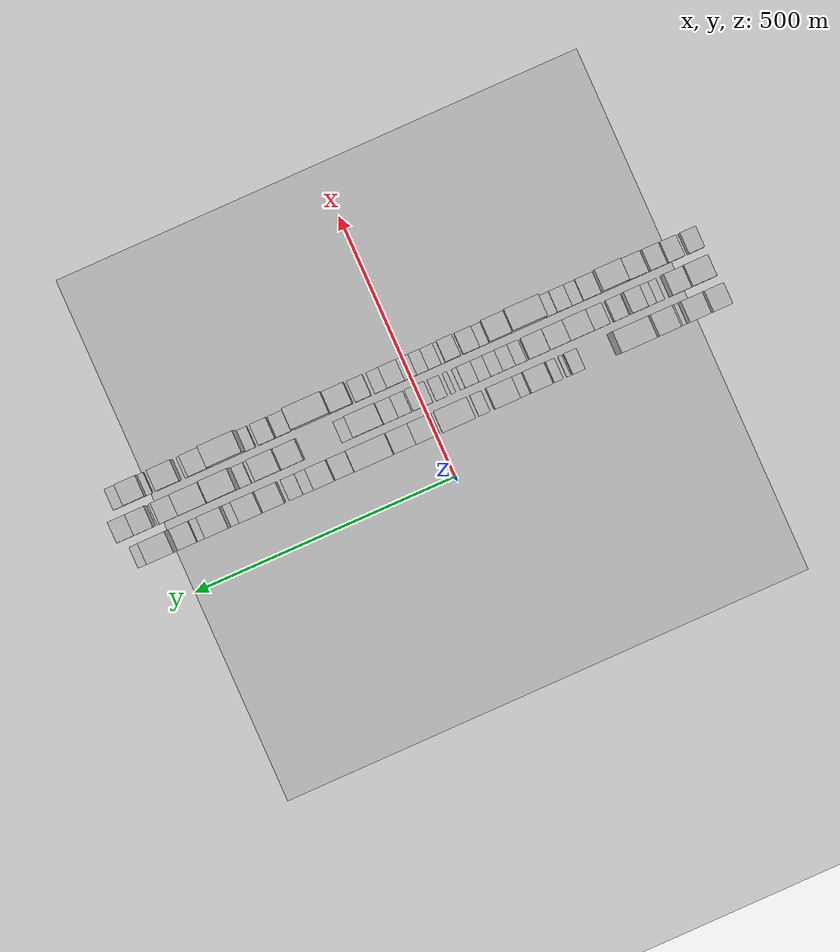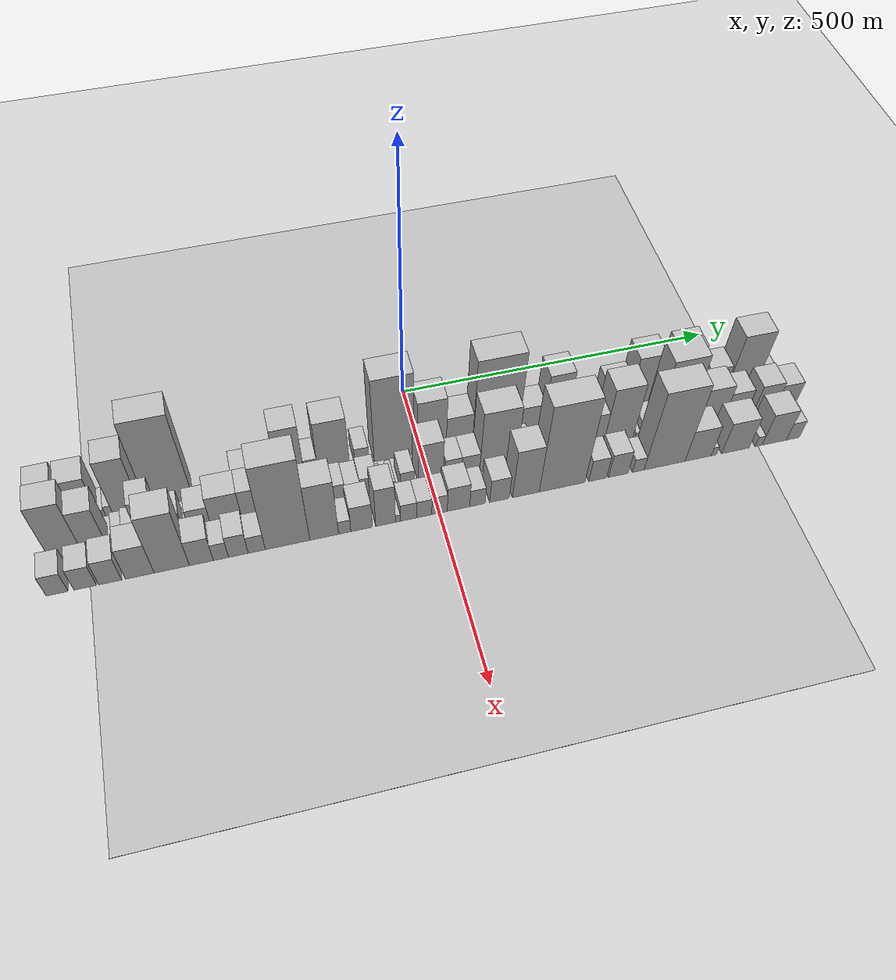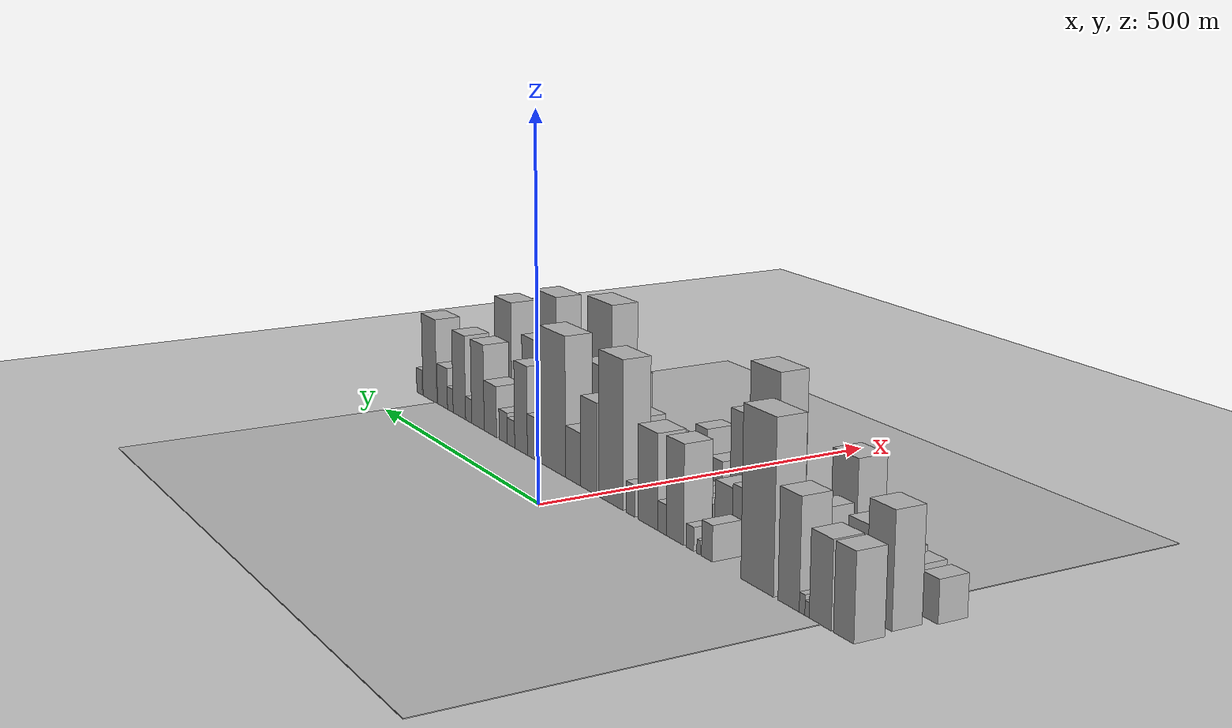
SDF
<?xml version="1.0" encoding="utf-8"?>

<sdf version="1.6">

   <world name="default">

      <gui fullscreen="0">

         <camera name="user_camera">

            <pose>-15 0 4.57585 0 0 0</pose>

            <view_controller>orbit</view_controller>

         </camera>

      </gui>

      <scene>

         <sky>

           <clouds>

             <speed>12</speed>

           </clouds>

         </sky>

         <ambient>0.4 0.4 0.4 1</ambient>

         <background>0.7 0.7 0.7 1</background>

         <shadows>1</shadows>

      </scene>

      <gravity>0 0 -9.8066</gravity>

      <magnetic_field>6e-06 2.3e-05 -4.2e-05</magnetic_field>

      <physics default="0" name="default_physics" type="ode">

         <ode>

            <solver>

               <type>quick</type>

               <iters>10</iters>

               <sor>1.0</sor>

               <use_dynamic_moi_rescaling>0</use_dynamic_moi_rescaling>

            </solver>

            <constraints>

               <cfm>0</cfm>

               <erp>0.2</erp>

               <contact_max_correcting_vel>100</contact_max_correcting_vel>

               <contact_surface_layer>0.001</contact_surface_layer>

            </constraints>

         </ode>

         <max_step_size>0.004</max_step_size>

         <real_time_factor>1</real_time_factor>

         <real_time_update_rate>250</real_time_update_rate>

      </physics>

      <light name="sun" type="directional">

         <cast_shadows>1</cast_shadows>

         <pose>0 0 10 0 0 0</pose>

         <diffuse>0.8 0.8 0.8 1</diffuse>

         <specular>0.2 0.2 0.2 1</specular>

         <attenuation>

            <range>1000</range>

            <constant>0.9</constant>

            <linear>0.01</linear>

            <quadratic>0.001</quadratic>

         </attenuation>

         <direction>-0.5 0.1 -0.9</direction>

      </light>

      <include>

         <name>ground_plane_1</name>

         <uri>model://HANNAS_ground_plane</uri>

         <pose>0 0 0  0 0 0</pose>

      </include>

      <include>

         <name>ground_plane_2</name>

         <uri>model://HANNAS_ground_plane</uri>

         <pose>100 0 0  0 0 0</pose>

      </include>

      <model name="building_1">

         <static>1</static>

         <pose frame="">100.0000 -541.8495 0 0.000000 0.000000 0.000000</pose>

         <link name="link">

            <pose frame="">0 0 51.00 0 0 0</pose>

            <collision name="collision">

               <geometry>

                  <box>

                     <size>40.0000 36.3010 102.0000</size>

                  </box>

               </geometry>

               <max_contacts>10</max_contacts>

               <surface>

                  <contact>

                     <ode/>

                  </contact>

                  <bounce/>

                  <friction>

                     <torsional>

                        <ode/>

                     </torsional>

                     <ode/>

                  </friction>

               </surface>

            </collision>

            <visual name="visual">

               <cast_shadows>0</cast_shadows>

               <geometry>

                  <box>

                     <size>40.0000 36.3010 102.0000</size>

                  </box>

               </geometry>

               <material>

                  <script>

                     <uri>model://HANNAS_wall/materials/scripts</uri>

                     <uri>model://HANNAS_wall/materials/textures</uri>

                     <name>vrc/HANNAS_wall</name>

                  </script>

               </material>

            </visual>

            <self_collide>0</self_collide>

            <enable_wind>0</enable_wind>

            <kinematic>0</kinematic>

         </link>

      </model>

      <model name="building_2">

         <static>1</static>

         <pose frame="">100.0000 -499.5074 0 0.000000 0.000000 0.000000</pose>

         <link name="link">

            <pose frame="">0 0 51.00 0 0 0</pose>

            <collision name="collision">

               <geometry>

                  <box>

                     <size>40.0000 40.3831 102.0000</size>

                  </box>

               </geometry>

               <max_contacts>10</max_contacts>

               <surface>

                  <contact>

                     <ode/>

                  </contact>

                  <bounce/>

                  <friction>

                     <torsional>

                        <ode/>

                     </torsional>

                     <ode/>

                  </friction>

               </surface>

            </collision>

            <visual name="visual">

               <cast_shadows>0</cast_shadows>

               <geometry>

                  <box>

                     <size>40.0000 40.3831 102.0000</size>

                  </box>

               </geometry>

               <material>

                  <script>

                     <uri>model://HANNAS_wall/materials/scripts</uri>

                     <uri>model://HANNAS_wall/materials/textures</uri>

                     <name>vrc/HANNAS_wall</name>

                  </script>

               </material>

            </visual>

            <self_collide>0</self_collide>

            <enable_wind>0</enable_wind>

            <kinematic>0</kinematic>

         </link>

      </model>

      <model name="building_3">

         <static>1</static>

         <pose frame="">100.0000 -475.2443 0 0.000000 0.000000 0.000000</pose>

         <link name="link">

            <pose frame="">0 0 9.00 0 0 0</pose>

            <collision name="collision">

               <geometry>

                  <box>

                     <size>40.0000 8.1431 18.0000</size>

                  </box>

               </geometry>

               <max_contacts>10</max_contacts>

               <surface>

                  <contact>

                     <ode/>

                  </contact>

                  <bounce/>

                  <friction>

                     <torsional>

                        <ode/>

                     </torsional>

                     <ode/>

                  </friction>

               </surface>

            </collision>

            <visual name="visual">

               <cast_shadows>0</cast_shadows>

               <geometry>

                  <box>

                     <size>40.0000 8.1431 18.0000</size>

                  </box>

               </geometry>

               <material>

                  <script>

                     <uri>model://HANNAS_wall/materials/scripts</uri>

                     <uri>model://HANNAS_wall/materials/textures</uri>

                     <name>vrc/HANNAS_wall</name>

                  </script>

               </material>

            </visual>

            <self_collide>0</self_collide>

            <enable_wind>0</enable_wind>

            <kinematic>0</kinematic>

         </link>

      </model>

      <model name="building_4">

         <static>1</static>

         <pose frame="">100.0000 -465.8494 0 0.000000 0.000000 0.000000</pose>

         <link name="link">

            <pose frame="">0 0 12.00 0 0 0</pose>

            <collision name="collision">

               <geometry>

                  <box>

                     <size>40.0000 10.6468 24.0000</size>

                  </box>

               </geometry>

               <max_contacts>10</max_contacts>

               <surface>

                  <contact>

                     <ode/>

                  </contact>

                  <bounce/>

                  <friction>

                     <torsional>

                        <ode/>

                     </torsional>

                     <ode/>

                  </friction>

               </surface>

            </collision>

            <visual name="visual">

               <cast_shadows>0</cast_shadows>

               <geometry>

                  <box>

                     <size>40.0000 10.6468 24.0000</size>

                  </box>

               </geometry>

               <material>

                  <script>

                     <uri>model://HANNAS_wall/materials/scripts</uri>

                     <uri>model://HANNAS_wall/materials/textures</uri>

                     <name>vrc/HANNAS_wall</name>

                  </script>

               </material>

            </visual>

            <self_collide>0</self_collide>

            <enable_wind>0</enable_wind>

            <kinematic>0</kinematic>

         </link>

      </model>

      <model name="building_5">

         <static>1</static>

         <pose frame="">100.0000 -440.0433 0 0.000000 0.000000 0.000000</pose>

         <link name="link">

            <pose frame="">0 0 66.00 0 0 0</pose>

            <collision name="collision">

               <geometry>

                  <box>

                     <size>40.0000 40.9655 132.0000</size>

                  </box>

               </geometry>

               <max_contacts>10</max_contacts>

               <surface>

                  <contact>

                     <ode/>

                  </contact>

                  <bounce/>

                  <friction>

                     <torsional>

                        <ode/>

                     </torsional>

                     <ode/>

                  </friction>

               </surface>

            </collision>

            <visual name="visual">

               <cast_shadows>0</cast_shadows>

               <geometry>

                  <box>

                     <size>40.0000 40.9655 132.0000</size>

                  </box>

               </geometry>

               <material>

                  <script>

                     <uri>model://HANNAS_wall/materials/scripts</uri>

                     <uri>model://HANNAS_wall/materials/textures</uri>

                     <name>vrc/HANNAS_wall</name>

                  </script>

               </material>

            </visual>

            <self_collide>0</self_collide>

            <enable_wind>0</enable_wind>

            <kinematic>0</kinematic>

         </link>

      </model>

      <model name="building_6">

         <static>1</static>

         <pose frame="">100.0000 -377.4662 0 0.000000 0.000000 0.000000</pose>

         <link name="link">

            <pose frame="">0 0 103.50 0 0 0</pose>

            <collision name="collision">

               <geometry>

                  <box>

                     <size>40.0000 66.1885 207.0000</size>

                  </box>

               </geometry>

               <max_contacts>10</max_contacts>

               <surface>

                  <contact>

                     <ode/>

                  </contact>

                  <bounce/>

                  <friction>

                     <torsional>

                        <ode/>

                     </torsional>

                     <ode/>

                  </friction>

               </surface>

            </collision>

            <visual name="visual">

               <cast_shadows>0</cast_shadows>

               <geometry>

                  <box>

                     <size>40.0000 66.1885 207.0000</size>

                  </box>

               </geometry>

               <material>

                  <script>

                     <uri>model://HANNAS_wall/materials/scripts</uri>

                     <uri>model://HANNAS_wall/materials/textures</uri>

                     <name>vrc/HANNAS_wall</name>

                  </script>

               </material>

            </visual>

            <self_collide>0</self_collide>

            <enable_wind>0</enable_wind>

            <kinematic>0</kinematic>

         </link>

      </model>

      <model name="building_7">

         <static>1</static>

         <pose frame="">100.0000 -271.7375 0 0.000000 0.000000 0.000000</pose>

         <link name="link">

            <pose frame="">0 0 22.50 0 0 0</pose>

            <collision name="collision">

               <geometry>

                  <box>

                     <size>40.0000 23.7564 45.0000</size>

                  </box>

               </geometry>

               <max_contacts>10</max_contacts>

               <surface>

                  <contact>

                     <ode/>

                  </contact>

                  <bounce/>

                  <friction>

                     <torsional>

                        <ode/>

                     </torsional>

                     <ode/>

                  </friction>

               </surface>

            </collision>

            <visual name="visual">

               <cast_shadows>0</cast_shadows>

               <geometry>

                  <box>

                     <size>40.0000 23.7564 45.0000</size>

                  </box>

               </geometry>

               <material>

                  <script>

                     <uri>model://HANNAS_wall/materials/scripts</uri>

                     <uri>model://HANNAS_wall/materials/textures</uri>

                     <name>vrc/HANNAS_wall</name>

                  </script>

               </material>

            </visual>

            <self_collide>0</self_collide>

            <enable_wind>0</enable_wind>

            <kinematic>0</kinematic>

         </link>

      </model>

      <model name="building_8">

         <static>1</static>

         <pose frame="">100.0000 -253.1174 0 0.000000 0.000000 0.000000</pose>

         <link name="link">

            <pose frame="">0 0 9.00 0 0 0</pose>

            <collision name="collision">

               <geometry>

                  <box>

                     <size>40.0000 7.4837 18.0000</size>

                  </box>

               </geometry>

               <max_contacts>10</max_contacts>

               <surface>

                  <contact>

                     <ode/>

                  </contact>

                  <bounce/>

                  <friction>

                     <torsional>

                        <ode/>

                     </torsional>

                     <ode/>

                  </friction>

               </surface>

            </collision>

            <visual name="visual">

               <cast_shadows>0</cast_shadows>

               <geometry>

                  <box>

                     <size>40.0000 7.4837 18.0000</size>

                  </box>

               </geometry>

               <material>

                  <script>

                     <uri>model://HANNAS_wall/materials/scripts</uri>

                     <uri>model://HANNAS_wall/materials/textures</uri>

                     <name>vrc/HANNAS_wall</name>

                  </script>

               </material>

            </visual>

            <self_collide>0</self_collide>

            <enable_wind>0</enable_wind>

            <kinematic>0</kinematic>

         </link>

      </model>

      <model name="building_9">

         <static>1</static>

         <pose frame="">100.0000 -233.8232 0 0.000000 0.000000 0.000000</pose>

         <link name="link">

            <pose frame="">0 0 15.00 0 0 0</pose>

            <collision name="collision">

               <geometry>

                  <box>

                     <size>40.0000 17.1046 30.0000</size>

                  </box>

               </geometry>

               <max_contacts>10</max_contacts>

               <surface>

                  <contact>

                     <ode/>

                  </contact>

                  <bounce/>

                  <friction>

                     <torsional>

                        <ode/>

                     </torsional>

                     <ode/>

                  </friction>

               </surface>

            </collision>

            <visual name="visual">

               <cast_shadows>0</cast_shadows>

               <geometry>

                  <box>

                     <size>40.0000 17.1046 30.0000</size>

                  </box>

               </geometry>

               <material>

                  <script>

                     <uri>model://HANNAS_wall/materials/scripts</uri>

                     <uri>model://HANNAS_wall/materials/textures</uri>

                     <name>vrc/HANNAS_wall</name>

                  </script>

               </material>

            </visual>

            <self_collide>0</self_collide>

            <enable_wind>0</enable_wind>

            <kinematic>0</kinematic>

         </link>

      </model>

      <model name="building_10">

         <static>1</static>

         <pose frame="">100.0000 -199.1108 0 0.000000 0.000000 0.000000</pose>

         <link name="link">

            <pose frame="">0 0 63.00 0 0 0</pose>

            <collision name="collision">

               <geometry>

                  <box>

                     <size>40.0000 40.3202 126.0000</size>

                  </box>

               </geometry>

               <max_contacts>10</max_contacts>

               <surface>

                  <contact>

                     <ode/>

                  </contact>

                  <bounce/>

                  <friction>

                     <torsional>

                        <ode/>

                     </torsional>

                     <ode/>

                  </friction>

               </surface>

            </collision>

            <visual name="visual">

               <cast_shadows>0</cast_shadows>

               <geometry>

                  <box>

                     <size>40.0000 40.3202 126.0000</size>

                  </box>

               </geometry>

               <material>

                  <script>

                     <uri>model://HANNAS_wall/materials/scripts</uri>

                     <uri>model://HANNAS_wall/materials/textures</uri>

                     <name>vrc/HANNAS_wall</name>

                  </script>

               </material>

            </visual>

            <self_collide>0</self_collide>

            <enable_wind>0</enable_wind>

            <kinematic>0</kinematic>

         </link>

      </model>

      <model name="building_11">

         <static>1</static>

         <pose frame="">100.0000 -168.6523 0 0.000000 0.000000 0.000000</pose>

         <link name="link">

            <pose frame="">0 0 19.50 0 0 0</pose>

            <collision name="collision">

               <geometry>

                  <box>

                     <size>40.0000 20.5967 39.0000</size>

                  </box>

               </geometry>

               <max_contacts>10</max_contacts>

               <surface>

                  <contact>

                     <ode/>

                  </contact>

                  <bounce/>

                  <friction>

                     <torsional>

                        <ode/>

                     </torsional>

                     <ode/>

                  </friction>

               </surface>

            </collision>

            <visual name="visual">

               <cast_shadows>0</cast_shadows>

               <geometry>

                  <box>

                     <size>40.0000 20.5967 39.0000</size>

                  </box>

               </geometry>

               <material>

                  <script>

                     <uri>model://HANNAS_wall/materials/scripts</uri>

                     <uri>model://HANNAS_wall/materials/textures</uri>

                     <name>vrc/HANNAS_wall</name>

                  </script>

               </material>

            </visual>

            <self_collide>0</self_collide>

            <enable_wind>0</enable_wind>

            <kinematic>0</kinematic>

         </link>

      </model>

      <model name="building_12">

         <static>1</static>

         <pose frame="">100.0000 -134.3191 0 0.000000 0.000000 0.000000</pose>

         <link name="link">

            <pose frame="">0 0 61.50 0 0 0</pose>

            <collision name="collision">

               <geometry>

                  <box>

                     <size>40.0000 48.0697 123.0000</size>

                  </box>

               </geometry>

               <max_contacts>10</max_contacts>

               <surface>

                  <contact>

                     <ode/>

                  </contact>

                  <bounce/>

                  <friction>

                     <torsional>

                        <ode/>

                     </torsional>

                     <ode/>

                  </friction>

               </surface>

            </collision>

            <visual name="visual">

               <cast_shadows>0</cast_shadows>

               <geometry>

                  <box>

                     <size>40.0000 48.0697 123.0000</size>

                  </box>

               </geometry>

               <material>

                  <script>

                     <uri>model://HANNAS_wall/materials/scripts</uri>

                     <uri>model://HANNAS_wall/materials/textures</uri>

                     <name>vrc/HANNAS_wall</name>

                  </script>

               </material>

            </visual>

            <self_collide>0</self_collide>

            <enable_wind>0</enable_wind>

            <kinematic>0</kinematic>

         </link>

      </model>

      <model name="building_13">

         <static>1</static>

         <pose frame="">100.0000 -91.4313 0 0.000000 0.000000 0.000000</pose>

         <link name="link">

            <pose frame="">0 0 21.00 0 0 0</pose>

            <collision name="collision">

               <geometry>

                  <box>

                     <size>40.0000 21.7058 42.0000</size>

                  </box>

               </geometry>

               <max_contacts>10</max_contacts>

               <surface>

                  <contact>

                     <ode/>

                  </contact>

                  <bounce/>

                  <friction>

                     <torsional>

                        <ode/>

                     </torsional>

                     <ode/>

                  </friction>

               </surface>

            </collision>

            <visual name="visual">

               <cast_shadows>0</cast_shadows>

               <geometry>

                  <box>

                     <size>40.0000 21.7058 42.0000</size>

                  </box>

               </geometry>

               <material>

                  <script>

                     <uri>model://HANNAS_wall/materials/scripts</uri>

                     <uri>model://HANNAS_wall/materials/textures</uri>

                     <name>vrc/HANNAS_wall</name>

                  </script>

               </material>

            </visual>

            <self_collide>0</self_collide>

            <enable_wind>0</enable_wind>

            <kinematic>0</kinematic>

         </link>

      </model>

      <model name="building_14">

         <static>1</static>

         <pose frame="">100.0000 -41.6882 0 0.000000 0.000000 0.000000</pose>

         <link name="link">

            <pose frame="">0 0 97.50 0 0 0</pose>

            <collision name="collision">

               <geometry>

                  <box>

                     <size>40.0000 61.7805 195.0000</size>

                  </box>

               </geometry>

               <max_contacts>10</max_contacts>

               <surface>

                  <contact>

                     <ode/>

                  </contact>

                  <bounce/>

                  <friction>

                     <torsional>

                        <ode/>

                     </torsional>

                     <ode/>

                  </friction>

               </surface>

            </collision>

            <visual name="visual">

               <cast_shadows>0</cast_shadows>

               <geometry>

                  <box>

                     <size>40.0000 61.7805 195.0000</size>

                  </box>

               </geometry>

               <material>

                  <script>

                     <uri>model://HANNAS_wall/materials/scripts</uri>

                     <uri>model://HANNAS_wall/materials/textures</uri>

                     <name>vrc/HANNAS_wall</name>

                  </script>

               </material>

            </visual>

            <self_collide>0</self_collide>

            <enable_wind>0</enable_wind>

            <kinematic>0</kinematic>

         </link>

      </model>

      <model name="building_15">

         <static>1</static>

         <pose frame="">100.0000 16.6368 0 0.000000 0.000000 0.000000</pose>

         <link name="link">

            <pose frame="">0 0 61.50 0 0 0</pose>

            <collision name="collision">

               <geometry>

                  <box>

                     <size>40.0000 44.8695 123.0000</size>

                  </box>

               </geometry>

               <max_contacts>10</max_contacts>

               <surface>

                  <contact>

                     <ode/>

                  </contact>

                  <bounce/>

                  <friction>

                     <torsional>

                        <ode/>

                     </torsional>

                     <ode/>

                  </friction>

               </surface>

            </collision>

            <visual name="visual">

               <cast_shadows>0</cast_shadows>

               <geometry>

                  <box>

                     <size>40.0000 44.8695 123.0000</size>

                  </box>

               </geometry>

               <material>

                  <script>

                     <uri>model://HANNAS_wall/materials/scripts</uri>

                     <uri>model://HANNAS_wall/materials/textures</uri>

                     <name>vrc/HANNAS_wall</name>

                  </script>

               </material>

            </visual>

            <self_collide>0</self_collide>

            <enable_wind>0</enable_wind>

            <kinematic>0</kinematic>

         </link>

      </model>

      <model name="building_16">

         <static>1</static>

         <pose frame="">100.0000 59.8555 0 0.000000 0.000000 0.000000</pose>

         <link name="link">

            <pose frame="">0 0 36.00 0 0 0</pose>

            <collision name="collision">

               <geometry>

                  <box>

                     <size>40.0000 41.5679 72.0000</size>

                  </box>

               </geometry>

               <max_contacts>10</max_contacts>

               <surface>

                  <contact>

                     <ode/>

                  </contact>

                  <bounce/>

                  <friction>

                     <torsional>

                        <ode/>

                     </torsional>

                     <ode/>

                  </friction>

               </surface>

            </collision>

            <visual name="visual">

               <cast_shadows>0</cast_shadows>

               <geometry>

                  <box>

                     <size>40.0000 41.5679 72.0000</size>

                  </box>

               </geometry>

               <material>

                  <script>

                     <uri>model://HANNAS_wall/materials/scripts</uri>

                     <uri>model://HANNAS_wall/materials/textures</uri>

                     <name>vrc/HANNAS_wall</name>

                  </script>

               </material>

            </visual>

            <self_collide>0</self_collide>

            <enable_wind>0</enable_wind>

            <kinematic>0</kinematic>

         </link>

      </model>

      <model name="building_17">

         <static>1</static>

         <pose frame="">100.0000 117.0593 0 0.000000 0.000000 0.000000</pose>

         <link name="link">

            <pose frame="">0 0 96.00 0 0 0</pose>

            <collision name="collision">

               <geometry>

                  <box>

                     <size>40.0000 72.8397 192.0000</size>

                  </box>

               </geometry>

               <max_contacts>10</max_contacts>

               <surface>

                  <contact>

                     <ode/>

                  </contact>

                  <bounce/>

                  <friction>

                     <torsional>

                        <ode/>

                     </torsional>

                     <ode/>

                  </friction>

               </surface>

            </collision>

            <visual name="visual">

               <cast_shadows>0</cast_shadows>

               <geometry>

                  <box>

                     <size>40.0000 72.8397 192.0000</size>

                  </box>

               </geometry>

               <material>

                  <script>

                     <uri>model://HANNAS_wall/materials/scripts</uri>

                     <uri>model://HANNAS_wall/materials/textures</uri>

                     <name>vrc/HANNAS_wall</name>

                  </script>

               </material>

            </visual>

            <self_collide>0</self_collide>

            <enable_wind>0</enable_wind>

            <kinematic>0</kinematic>

         </link>

      </model>

      <model name="building_18">

         <static>1</static>

         <pose frame="">100.0000 175.2094 0 0.000000 0.000000 0.000000</pose>

         <link name="link">

            <pose frame="">0 0 30.00 0 0 0</pose>

            <collision name="collision">

               <geometry>

                  <box>

                     <size>40.0000 35.4605 60.0000</size>

                  </box>

               </geometry>

               <max_contacts>10</max_contacts>

               <surface>

                  <contact>

                     <ode/>

                  </contact>

                  <bounce/>

                  <friction>

                     <torsional>

                        <ode/>

                     </torsional>

                     <ode/>

                  </friction>

               </surface>

            </collision>

            <visual name="visual">

               <cast_shadows>0</cast_shadows>

               <geometry>

                  <box>

                     <size>40.0000 35.4605 60.0000</size>

                  </box>

               </geometry>

               <material>

                  <script>

                     <uri>model://HANNAS_wall/materials/scripts</uri>

                     <uri>model://HANNAS_wall/materials/textures</uri>

                     <name>vrc/HANNAS_wall</name>

                  </script>

               </material>

            </visual>

            <self_collide>0</self_collide>

            <enable_wind>0</enable_wind>

            <kinematic>0</kinematic>

         </link>

      </model>

      <model name="building_19">

         <static>1</static>

         <pose frame="">100.0000 212.4825 0 0.000000 0.000000 0.000000</pose>

         <link name="link">

            <pose frame="">0 0 63.00 0 0 0</pose>

            <collision name="collision">

               <geometry>

                  <box>

                     <size>40.0000 39.0856 126.0000</size>

                  </box>

               </geometry>

               <max_contacts>10</max_contacts>

               <surface>

                  <contact>

                     <ode/>

                  </contact>

                  <bounce/>

                  <friction>

                     <torsional>

                        <ode/>

                     </torsional>

                     <ode/>

                  </friction>

               </surface>

            </collision>

            <visual name="visual">

               <cast_shadows>0</cast_shadows>

               <geometry>

                  <box>

                     <size>40.0000 39.0856 126.0000</size>

                  </box>

               </geometry>

               <material>

                  <script>

                     <uri>model://HANNAS_wall/materials/scripts</uri>

                     <uri>model://HANNAS_wall/materials/textures</uri>

                     <name>vrc/HANNAS_wall</name>

                  </script>

               </material>

            </visual>

            <self_collide>0</self_collide>

            <enable_wind>0</enable_wind>

            <kinematic>0</kinematic>

         </link>

      </model>

      <model name="building_20">

         <static>1</static>

         <pose frame="">100.0000 243.4756 0 0.000000 0.000000 0.000000</pose>

         <link name="link">

            <pose frame="">0 0 19.50 0 0 0</pose>

            <collision name="collision">

               <geometry>

                  <box>

                     <size>40.0000 22.9006 39.0000</size>

                  </box>

               </geometry>

               <max_contacts>10</max_contacts>

               <surface>

                  <contact>

                     <ode/>

                  </contact>

                  <bounce/>

                  <friction>

                     <torsional>

                        <ode/>

                     </torsional>

                     <ode/>

                  </friction>

               </surface>

            </collision>

            <visual name="visual">

               <cast_shadows>0</cast_shadows>

               <geometry>

                  <box>

                     <size>40.0000 22.9006 39.0000</size>

                  </box>

               </geometry>

               <material>

                  <script>

                     <uri>model://HANNAS_wall/materials/scripts</uri>

                     <uri>model://HANNAS_wall/materials/textures</uri>

                     <name>vrc/HANNAS_wall</name>

                  </script>

               </material>

            </visual>

            <self_collide>0</self_collide>

            <enable_wind>0</enable_wind>

            <kinematic>0</kinematic>

         </link>

      </model>

      <model name="building_21">

         <static>1</static>

         <pose frame="">100.0000 268.1488 0 0.000000 0.000000 0.000000</pose>

         <link name="link">

            <pose frame="">0 0 22.50 0 0 0</pose>

            <collision name="collision">

               <geometry>

                  <box>

                     <size>40.0000 26.4457 45.0000</size>

                  </box>

               </geometry>

               <max_contacts>10</max_contacts>

               <surface>

                  <contact>

                     <ode/>

                  </contact>

                  <bounce/>

                  <friction>

                     <torsional>

                        <ode/>

                     </torsional>

                     <ode/>

                  </friction>

               </surface>

            </collision>

            <visual name="visual">

               <cast_shadows>0</cast_shadows>

               <geometry>

                  <box>

                     <size>40.0000 26.4457 45.0000</size>

                  </box>

               </geometry>

               <material>

                  <script>

                     <uri>model://HANNAS_wall/materials/scripts</uri>

                     <uri>model://HANNAS_wall/materials/textures</uri>

                     <name>vrc/HANNAS_wall</name>

                  </script>

               </material>

            </visual>

            <self_collide>0</self_collide>

            <enable_wind>0</enable_wind>

            <kinematic>0</kinematic>

         </link>

      </model>

      <model name="building_22">

         <static>1</static>

         <pose frame="">100.0000 309.7758 0 0.000000 0.000000 0.000000</pose>

         <link name="link">

            <pose frame="">0 0 37.50 0 0 0</pose>

            <collision name="collision">

               <geometry>

                  <box>

                     <size>40.0000 40.8084 75.0000</size>

                  </box>

               </geometry>

               <max_contacts>10</max_contacts>

               <surface>

                  <contact>

                     <ode/>

                  </contact>

                  <bounce/>

                  <friction>

                     <torsional>

                        <ode/>

                     </torsional>

                     <ode/>

                  </friction>

               </surface>

            </collision>

            <visual name="visual">

               <cast_shadows>0</cast_shadows>

               <geometry>

                  <box>

                     <size>40.0000 40.8084 75.0000</size>

                  </box>

               </geometry>

               <material>

                  <script>

                     <uri>model://HANNAS_wall/materials/scripts</uri>

                     <uri>model://HANNAS_wall/materials/textures</uri>

                     <name>vrc/HANNAS_wall</name>

                  </script>

               </material>

            </visual>

            <self_collide>0</self_collide>

            <enable_wind>0</enable_wind>

            <kinematic>0</kinematic>

         </link>

      </model>

      <model name="building_23">

         <static>1</static>

         <pose frame="">100.0000 351.2639 0 0.000000 0.000000 0.000000</pose>

         <link name="link">

            <pose frame="">0 0 63.00 0 0 0</pose>

            <collision name="collision">

               <geometry>

                  <box>

                     <size>40.0000 42.1678 126.0000</size>

                  </box>

               </geometry>

               <max_contacts>10</max_contacts>

               <surface>

                  <contact>

                     <ode/>

                  </contact>

                  <bounce/>

                  <friction>

                     <torsional>

                        <ode/>

                     </torsional>

                     <ode/>

                  </friction>

               </surface>

            </collision>

            <visual name="visual">

               <cast_shadows>0</cast_shadows>

               <geometry>

                  <box>

                     <size>40.0000 42.1678 126.0000</size>

                  </box>

               </geometry>

               <material>

                  <script>

                     <uri>model://HANNAS_wall/materials/scripts</uri>

                     <uri>model://HANNAS_wall/materials/textures</uri>

                     <name>vrc/HANNAS_wall</name>

                  </script>

               </material>

            </visual>

            <self_collide>0</self_collide>

            <enable_wind>0</enable_wind>

            <kinematic>0</kinematic>

         </link>

      </model>

      <model name="building_24">

         <static>1</static>

         <pose frame="">100.0000 382.6859 0 0.000000 0.000000 0.000000</pose>

         <link name="link">

            <pose frame="">0 0 18.00 0 0 0</pose>

            <collision name="collision">

               <geometry>

                  <box>

                     <size>40.0000 20.6761 36.0000</size>

                  </box>

               </geometry>

               <max_contacts>10</max_contacts>

               <surface>

                  <contact>

                     <ode/>

                  </contact>

                  <bounce/>

                  <friction>

                     <torsional>

                        <ode/>

                     </torsional>

                     <ode/>

                  </friction>

               </surface>

            </collision>

            <visual name="visual">

               <cast_shadows>0</cast_shadows>

               <geometry>

                  <box>

                     <size>40.0000 20.6761 36.0000</size>

                  </box>

               </geometry>

               <material>

                  <script>

                     <uri>model://HANNAS_wall/materials/scripts</uri>

                     <uri>model://HANNAS_wall/materials/textures</uri>

                     <name>vrc/HANNAS_wall</name>

                  </script>

               </material>

            </visual>

            <self_collide>0</self_collide>

            <enable_wind>0</enable_wind>

            <kinematic>0</kinematic>

         </link>

      </model>

      <model name="building_25">

         <static>1</static>

         <pose frame="">100.0000 414.9001 0 0.000000 0.000000 0.000000</pose>

         <link name="link">

            <pose frame="">0 0 63.00 0 0 0</pose>

            <collision name="collision">

               <geometry>

                  <box>

                     <size>40.0000 43.7524 126.0000</size>

                  </box>

               </geometry>

               <max_contacts>10</max_contacts>

               <surface>

                  <contact>

                     <ode/>

                  </contact>

                  <bounce/>

                  <friction>

                     <torsional>

                        <ode/>

                     </torsional>

                     <ode/>

                  </friction>

               </surface>

            </collision>

            <visual name="visual">

               <cast_shadows>0</cast_shadows>

               <geometry>

                  <box>

                     <size>40.0000 43.7524 126.0000</size>

                  </box>

               </geometry>

               <material>

                  <script>

                     <uri>model://HANNAS_wall/materials/scripts</uri>

                     <uri>model://HANNAS_wall/materials/textures</uri>

                     <name>vrc/HANNAS_wall</name>

                  </script>

               </material>

            </visual>

            <self_collide>0</self_collide>

            <enable_wind>0</enable_wind>

            <kinematic>0</kinematic>

         </link>

      </model>

      <model name="building_26">

         <static>1</static>

         <pose frame="">100.0000 446.7177 0 0.000000 0.000000 0.000000</pose>

         <link name="link">

            <pose frame="">0 0 18.00 0 0 0</pose>

            <collision name="collision">

               <geometry>

                  <box>

                     <size>40.0000 19.8828 36.0000</size>

                  </box>

               </geometry>

               <max_contacts>10</max_contacts>

               <surface>

                  <contact>

                     <ode/>

                  </contact>

                  <bounce/>

                  <friction>

                     <torsional>

                        <ode/>

                     </torsional>

                     <ode/>

                  </friction>

               </surface>

            </collision>

            <visual name="visual">

               <cast_shadows>0</cast_shadows>

               <geometry>

                  <box>

                     <size>40.0000 19.8828 36.0000</size>

                  </box>

               </geometry>

               <material>

                  <script>

                     <uri>model://HANNAS_wall/materials/scripts</uri>

                     <uri>model://HANNAS_wall/materials/textures</uri>

                     <name>vrc/HANNAS_wall</name>

                  </script>

               </material>

            </visual>

            <self_collide>0</self_collide>

            <enable_wind>0</enable_wind>

            <kinematic>0</kinematic>

         </link>

      </model>

      <model name="building_27">

         <static>1</static>

         <pose frame="">100.0000 474.7866 0 0.000000 0.000000 0.000000</pose>

         <link name="link">

            <pose frame="">0 0 31.50 0 0 0</pose>

            <collision name="collision">

               <geometry>

                  <box>

                     <size>40.0000 36.2548 63.0000</size>

                  </box>

               </geometry>

               <max_contacts>10</max_contacts>

               <surface>

                  <contact>

                     <ode/>

                  </contact>

                  <bounce/>

                  <friction>

                     <torsional>

                        <ode/>

                     </torsional>

                     <ode/>

                  </friction>

               </surface>

            </collision>

            <visual name="visual">

               <cast_shadows>0</cast_shadows>

               <geometry>

                  <box>

                     <size>40.0000 36.2548 63.0000</size>

                  </box>

               </geometry>

               <material>

                  <script>

                     <uri>model://HANNAS_wall/materials/scripts</uri>

                     <uri>model://HANNAS_wall/materials/textures</uri>

                     <name>vrc/HANNAS_wall</name>

                  </script>

               </material>

            </visual>

            <self_collide>0</self_collide>

            <enable_wind>0</enable_wind>

            <kinematic>0</kinematic>

         </link>

      </model>

      <model name="building_28">

         <static>1</static>

         <pose frame="">100.0000 521.2659 0 0.000000 0.000000 0.000000</pose>

         <link name="link">

            <pose frame="">0 0 64.50 0 0 0</pose>

            <collision name="collision">

               <geometry>

                  <box>

                     <size>40.0000 50.7038 129.0000</size>

                  </box>

               </geometry>

               <max_contacts>10</max_contacts>

               <surface>

                  <contact>

                     <ode/>

                  </contact>

                  <bounce/>

                  <friction>

                     <torsional>

                        <ode/>

                     </torsional>

                     <ode/>

                  </friction>

               </surface>

            </collision>

            <visual name="visual">

               <cast_shadows>0</cast_shadows>

               <geometry>

                  <box>

                     <size>40.0000 50.7038 129.0000</size>

                  </box>

               </geometry>

               <material>

                  <script>

                     <uri>model://HANNAS_wall/materials/scripts</uri>

                     <uri>model://HANNAS_wall/materials/textures</uri>

                     <name>vrc/HANNAS_wall</name>

                  </script>

               </material>

            </visual>

            <self_collide>0</self_collide>

            <enable_wind>0</enable_wind>

            <kinematic>0</kinematic>

         </link>

      </model>

      <model name="building_29">

         <static>1</static>

         <pose frame="">100.0000 559.9831 0 0.000000 0.000000 0.000000</pose>

         <link name="link">

            <pose frame="">0 0 19.50 0 0 0</pose>

            <collision name="collision">

               <geometry>

                  <box>

                     <size>40.0000 20.7306 39.0000</size>

                  </box>

               </geometry>

               <max_contacts>10</max_contacts>

               <surface>

                  <contact>

                     <ode/>

                  </contact>

                  <bounce/>

                  <friction>

                     <torsional>

                        <ode/>

                     </torsional>

                     <ode/>

                  </friction>

               </surface>

            </collision>

            <visual name="visual">

               <cast_shadows>0</cast_shadows>

               <geometry>

                  <box>

                     <size>40.0000 20.7306 39.0000</size>

                  </box>

               </geometry>

               <material>

                  <script>

                     <uri>model://HANNAS_wall/materials/scripts</uri>

                     <uri>model://HANNAS_wall/materials/textures</uri>

                     <name>vrc/HANNAS_wall</name>

                  </script>

               </material>

            </visual>

            <self_collide>0</self_collide>

            <enable_wind>0</enable_wind>

            <kinematic>0</kinematic>

         </link>

      </model>

      <model name="building_30">

         <static>1</static>

         <pose frame="">155.0000 -529.2739 0 0.000000 0.000000 0.000000</pose>

         <link name="link">

            <pose frame="">0 0 67.50 0 0 0</pose>

            <collision name="collision">

               <geometry>

                  <box>

                     <size>40.0000 45.4523 135.0000</size>

                  </box>

               </geometry>

               <max_contacts>10</max_contacts>

               <surface>

                  <contact>

                     <ode/>

                  </contact>

                  <bounce/>

                  <friction>

                     <torsional>

                        <ode/>

                     </torsional>

                     <ode/>

                  </friction>

               </surface>

            </collision>

            <visual name="visual">

               <cast_shadows>0</cast_shadows>

               <geometry>

                  <box>

                     <size>40.0000 45.4523 135.0000</size>

                  </box>

               </geometry>

               <material>

                  <script>

                     <uri>model://HANNAS_wall/materials/scripts</uri>

                     <uri>model://HANNAS_wall/materials/textures</uri>

                     <name>vrc/HANNAS_wall</name>

                  </script>

               </material>

            </visual>

            <self_collide>0</self_collide>

            <enable_wind>0</enable_wind>

            <kinematic>0</kinematic>

         </link>

      </model>

      <model name="building_31">

         <static>1</static>

         <pose frame="">155.0000 -488.7142 0 0.000000 0.000000 0.000000</pose>

         <link name="link">

            <pose frame="">0 0 52.50 0 0 0</pose>

            <collision name="collision">

               <geometry>

                  <box>

                     <size>40.0000 35.6670 105.0000</size>

                  </box>

               </geometry>

               <max_contacts>10</max_contacts>

               <surface>

                  <contact>

                     <ode/>

                  </contact>

                  <bounce/>

                  <friction>

                     <torsional>

                        <ode/>

                     </torsional>

                     <ode/>

                  </friction>

               </surface>

            </collision>

            <visual name="visual">

               <cast_shadows>0</cast_shadows>

               <geometry>

                  <box>

                     <size>40.0000 35.6670 105.0000</size>

                  </box>

               </geometry>

               <material>

                  <script>

                     <uri>model://HANNAS_wall/materials/scripts</uri>

                     <uri>model://HANNAS_wall/materials/textures</uri>

                     <name>vrc/HANNAS_wall</name>

                  </script>

               </material>

            </visual>

            <self_collide>0</self_collide>

            <enable_wind>0</enable_wind>

            <kinematic>0</kinematic>

         </link>

      </model>

      <model name="building_32">

         <static>1</static>

         <pose frame="">155.0000 -453.1884 0 0.000000 0.000000 0.000000</pose>

         <link name="link">

            <pose frame="">0 0 15.00 0 0 0</pose>

            <collision name="collision">

               <geometry>

                  <box>

                     <size>40.0000 15.3847 30.0000</size>

                  </box>

               </geometry>

               <max_contacts>10</max_contacts>

               <surface>

                  <contact>

                     <ode/>

                  </contact>

                  <bounce/>

                  <friction>

                     <torsional>

                        <ode/>

                     </torsional>

                     <ode/>

                  </friction>

               </surface>

            </collision>

            <visual name="visual">

               <cast_shadows>0</cast_shadows>

               <geometry>

                  <box>

                     <size>40.0000 15.3847 30.0000</size>

                  </box>

               </geometry>

               <material>

                  <script>

                     <uri>model://HANNAS_wall/materials/scripts</uri>

                     <uri>model://HANNAS_wall/materials/textures</uri>

                     <name>vrc/HANNAS_wall</name>

                  </script>

               </material>

            </visual>

            <self_collide>0</self_collide>

            <enable_wind>0</enable_wind>

            <kinematic>0</kinematic>

         </link>

      </model>

      <model name="building_33">

         <static>1</static>

         <pose frame="">155.0000 -435.5298 0 0.000000 0.000000 0.000000</pose>

         <link name="link">

            <pose frame="">0 0 18.00 0 0 0</pose>

            <collision name="collision">

               <geometry>

                  <box>

                     <size>40.0000 19.9325 36.0000</size>

                  </box>

               </geometry>

               <max_contacts>10</max_contacts>

               <surface>

                  <contact>

                     <ode/>

                  </contact>

                  <bounce/>

                  <friction>

                     <torsional>

                        <ode/>

                     </torsional>

                     <ode/>

                  </friction>

               </surface>

            </collision>

            <visual name="visual">

               <cast_shadows>0</cast_shadows>

               <geometry>

                  <box>

                     <size>40.0000 19.9325 36.0000</size>

                  </box>

               </geometry>

               <material>

                  <script>

                     <uri>model://HANNAS_wall/materials/scripts</uri>

                     <uri>model://HANNAS_wall/materials/textures</uri>

                     <name>vrc/HANNAS_wall</name>

                  </script>

               </material>

            </visual>

            <self_collide>0</self_collide>

            <enable_wind>0</enable_wind>

            <kinematic>0</kinematic>

         </link>

      </model>

      <model name="building_34">

         <static>1</static>

         <pose frame="">155.0000 -410.4630 0 0.000000 0.000000 0.000000</pose>

         <link name="link">

            <pose frame="">0 0 49.50 0 0 0</pose>

            <collision name="collision">

               <geometry>

                  <box>

                     <size>40.0000 30.2012 99.0000</size>

                  </box>

               </geometry>

               <max_contacts>10</max_contacts>

               <surface>

                  <contact>

                     <ode/>

                  </contact>

                  <bounce/>

                  <friction>

                     <torsional>

                        <ode/>

                     </torsional>

                     <ode/>

                  </friction>

               </surface>

            </collision>

            <visual name="visual">

               <cast_shadows>0</cast_shadows>

               <geometry>

                  <box>

                     <size>40.0000 30.2012 99.0000</size>

                  </box>

               </geometry>

               <material>

                  <script>

                     <uri>model://HANNAS_wall/materials/scripts</uri>

                     <uri>model://HANNAS_wall/materials/textures</uri>

                     <name>vrc/HANNAS_wall</name>

                  </script>

               </material>

            </visual>

            <self_collide>0</self_collide>

            <enable_wind>0</enable_wind>

            <kinematic>0</kinematic>

         </link>

      </model>

      <model name="building_35">

         <static>1</static>

         <pose frame="">155.0000 -377.3726 0 0.000000 0.000000 0.000000</pose>

         <link name="link">

            <pose frame="">0 0 27.00 0 0 0</pose>

            <collision name="collision">

               <geometry>

                  <box>

                     <size>40.0000 27.9795 54.0000</size>

                  </box>

               </geometry>

               <max_contacts>10</max_contacts>

               <surface>

                  <contact>

                     <ode/>

                  </contact>

                  <bounce/>

                  <friction>

                     <torsional>

                        <ode/>

                     </torsional>

                     <ode/>

                  </friction>

               </surface>

            </collision>

            <visual name="visual">

               <cast_shadows>0</cast_shadows>

               <geometry>

                  <box>

                     <size>40.0000 27.9795 54.0000</size>

                  </box>

               </geometry>

               <material>

                  <script>

                     <uri>model://HANNAS_wall/materials/scripts</uri>

                     <uri>model://HANNAS_wall/materials/textures</uri>

                     <name>vrc/HANNAS_wall</name>

                  </script>

               </material>

            </visual>

            <self_collide>0</self_collide>

            <enable_wind>0</enable_wind>

            <kinematic>0</kinematic>

         </link>

      </model>

      <model name="building_36">

         <static>1</static>

         <pose frame="">155.0000 -339.8803 0 0.000000 0.000000 0.000000</pose>

         <link name="link">

            <pose frame="">0 0 27.00 0 0 0</pose>

            <collision name="collision">

               <geometry>

                  <box>

                     <size>40.0000 31.0051 54.0000</size>

                  </box>

               </geometry>

               <max_contacts>10</max_contacts>

               <surface>

                  <contact>

                     <ode/>

                  </contact>

                  <bounce/>

                  <friction>

                     <torsional>

                        <ode/>

                     </torsional>

                     <ode/>

                  </friction>

               </surface>

            </collision>

            <visual name="visual">

               <cast_shadows>0</cast_shadows>

               <geometry>

                  <box>

                     <size>40.0000 31.0051 54.0000</size>

                  </box>

               </geometry>

               <material>

                  <script>

                     <uri>model://HANNAS_wall/materials/scripts</uri>

                     <uri>model://HANNAS_wall/materials/textures</uri>

                     <name>vrc/HANNAS_wall</name>

                  </script>

               </material>

            </visual>

            <self_collide>0</self_collide>

            <enable_wind>0</enable_wind>

            <kinematic>0</kinematic>

         </link>

      </model>

      <model name="building_37">

         <static>1</static>

         <pose frame="">155.0000 -301.8928 0 0.000000 0.000000 0.000000</pose>

         <link name="link">

            <pose frame="">0 0 37.50 0 0 0</pose>

            <collision name="collision">

               <geometry>

                  <box>

                     <size>40.0000 44.9698 75.0000</size>

                  </box>

               </geometry>

               <max_contacts>10</max_contacts>

               <surface>

                  <contact>

                     <ode/>

                  </contact>

                  <bounce/>

                  <friction>

                     <torsional>

                        <ode/>

                     </torsional>

                     <ode/>

                  </friction>

               </surface>

            </collision>

            <visual name="visual">

               <cast_shadows>0</cast_shadows>

               <geometry>

                  <box>

                     <size>40.0000 44.9698 75.0000</size>

                  </box>

               </geometry>

               <material>

                  <script>

                     <uri>model://HANNAS_wall/materials/scripts</uri>

                     <uri>model://HANNAS_wall/materials/textures</uri>

                     <name>vrc/HANNAS_wall</name>

                  </script>

               </material>

            </visual>

            <self_collide>0</self_collide>

            <enable_wind>0</enable_wind>

            <kinematic>0</kinematic>

         </link>

      </model>

      <model name="building_38">

         <static>1</static>

         <pose frame="">155.0000 -259.9744 0 0.000000 0.000000 0.000000</pose>

         <link name="link">

            <pose frame="">0 0 37.50 0 0 0</pose>

            <collision name="collision">

               <geometry>

                  <box>

                     <size>40.0000 38.8671 75.0000</size>

                  </box>

               </geometry>

               <max_contacts>10</max_contacts>

               <surface>

                  <contact>

                     <ode/>

                  </contact>

                  <bounce/>

                  <friction>

                     <torsional>

                        <ode/>

                     </torsional>

                     <ode/>

                  </friction>

               </surface>

            </collision>

            <visual name="visual">

               <cast_shadows>0</cast_shadows>

               <geometry>

                  <box>

                     <size>40.0000 38.8671 75.0000</size>

                  </box>

               </geometry>

               <material>

                  <script>

                     <uri>model://HANNAS_wall/materials/scripts</uri>

                     <uri>model://HANNAS_wall/materials/textures</uri>

                     <name>vrc/HANNAS_wall</name>

                  </script>

               </material>

            </visual>

            <self_collide>0</self_collide>

            <enable_wind>0</enable_wind>

            <kinematic>0</kinematic>

         </link>

      </model>

      <model name="building_39">

         <static>1</static>

         <pose frame="">155.0000 -220.7351 0 0.000000 0.000000 0.000000</pose>

         <link name="link">

            <pose frame="">0 0 34.50 0 0 0</pose>

            <collision name="collision">

               <geometry>

                  <box>

                     <size>40.0000 39.6115 69.0000</size>

                  </box>

               </geometry>

               <max_contacts>10</max_contacts>

               <surface>

                  <contact>

                     <ode/>

                  </contact>

                  <bounce/>

                  <friction>

                     <torsional>

                        <ode/>

                     </torsional>

                     <ode/>

                  </friction>

               </surface>

            </collision>

            <visual name="visual">

               <cast_shadows>0</cast_shadows>

               <geometry>

                  <box>

                     <size>40.0000 39.6115 69.0000</size>

                  </box>

               </geometry>

               <material>

                  <script>

                     <uri>model://HANNAS_wall/materials/scripts</uri>

                     <uri>model://HANNAS_wall/materials/textures</uri>

                     <name>vrc/HANNAS_wall</name>

                  </script>

               </material>

            </visual>

            <self_collide>0</self_collide>

            <enable_wind>0</enable_wind>

            <kinematic>0</kinematic>

         </link>

      </model>

      <model name="building_40">

         <static>1</static>

         <pose frame="">155.0000 -186.2544 0 0.000000 0.000000 0.000000</pose>

         <link name="link">

            <pose frame="">0 0 18.00 0 0 0</pose>

            <collision name="collision">

               <geometry>

                  <box>

                     <size>40.0000 21.3499 36.0000</size>

                  </box>

               </geometry>

               <max_contacts>10</max_contacts>

               <surface>

                  <contact>

                     <ode/>

                  </contact>

                  <bounce/>

                  <friction>

                     <torsional>

                        <ode/>

                     </torsional>

                     <ode/>

                  </friction>

               </surface>

            </collision>

            <visual name="visual">

               <cast_shadows>0</cast_shadows>

               <geometry>

                  <box>

                     <size>40.0000 21.3499 36.0000</size>

                  </box>

               </geometry>

               <material>

                  <script>

                     <uri>model://HANNAS_wall/materials/scripts</uri>

                     <uri>model://HANNAS_wall/materials/textures</uri>

                     <name>vrc/HANNAS_wall</name>

                  </script>

               </material>

            </visual>

            <self_collide>0</self_collide>

            <enable_wind>0</enable_wind>

            <kinematic>0</kinematic>

         </link>

      </model>

      <model name="building_41">

         <static>1</static>

         <pose frame="">155.0000 -163.4120 0 0.000000 0.000000 0.000000</pose>

         <link name="link">

            <pose frame="">0 0 21.00 0 0 0</pose>

            <collision name="collision">

               <geometry>

                  <box>

                     <size>40.0000 24.3349 42.0000</size>

                  </box>

               </geometry>

               <max_contacts>10</max_contacts>

               <surface>

                  <contact>

                     <ode/>

                  </contact>

                  <bounce/>

                  <friction>

                     <torsional>

                        <ode/>

                     </torsional>

                     <ode/>

                  </friction>

               </surface>

            </collision>

            <visual name="visual">

               <cast_shadows>0</cast_shadows>

               <geometry>

                  <box>

                     <size>40.0000 24.3349 42.0000</size>

                  </box>

               </geometry>

               <material>

                  <script>

                     <uri>model://HANNAS_wall/materials/scripts</uri>

                     <uri>model://HANNAS_wall/materials/textures</uri>

                     <name>vrc/HANNAS_wall</name>

                  </script>

               </material>

            </visual>

            <self_collide>0</self_collide>

            <enable_wind>0</enable_wind>

            <kinematic>0</kinematic>

         </link>

      </model>

      <model name="building_42">

         <static>1</static>

         <pose frame="">155.0000 -139.5206 0 0.000000 0.000000 0.000000</pose>

         <link name="link">

            <pose frame="">0 0 21.00 0 0 0</pose>

            <collision name="collision">

               <geometry>

                  <box>

                     <size>40.0000 23.4479 42.0000</size>

                  </box>

               </geometry>

               <max_contacts>10</max_contacts>

               <surface>

                  <contact>

                     <ode/>

                  </contact>

                  <bounce/>

                  <friction>

                     <torsional>

                        <ode/>

                     </torsional>

                     <ode/>

                  </friction>

               </surface>

            </collision>

            <visual name="visual">

               <cast_shadows>0</cast_shadows>

               <geometry>

                  <box>

                     <size>40.0000 23.4479 42.0000</size>

                  </box>

               </geometry>

               <material>

                  <script>

                     <uri>model://HANNAS_wall/materials/scripts</uri>

                     <uri>model://HANNAS_wall/materials/textures</uri>

                     <name>vrc/HANNAS_wall</name>

                  </script>

               </material>

            </visual>

            <self_collide>0</self_collide>

            <enable_wind>0</enable_wind>

            <kinematic>0</kinematic>

         </link>

      </model>

      <model name="building_43">

         <static>1</static>

         <pose frame="">155.0000 -116.5061 0 0.000000 0.000000 0.000000</pose>

         <link name="link">

            <pose frame="">0 0 19.50 0 0 0</pose>

            <collision name="collision">

               <geometry>

                  <box>

                     <size>40.0000 22.5811 39.0000</size>

                  </box>

               </geometry>

               <max_contacts>10</max_contacts>

               <surface>

                  <contact>

                     <ode/>

                  </contact>

                  <bounce/>

                  <friction>

                     <torsional>

                        <ode/>

                     </torsional>

                     <ode/>

                  </friction>

               </surface>

            </collision>

            <visual name="visual">

               <cast_shadows>0</cast_shadows>

               <geometry>

                  <box>

                     <size>40.0000 22.5811 39.0000</size>

                  </box>

               </geometry>

               <material>

                  <script>

                     <uri>model://HANNAS_wall/materials/scripts</uri>

                     <uri>model://HANNAS_wall/materials/textures</uri>

                     <name>vrc/HANNAS_wall</name>

                  </script>

               </material>

            </visual>

            <self_collide>0</self_collide>

            <enable_wind>0</enable_wind>

            <kinematic>0</kinematic>

         </link>

      </model>

      <model name="building_44">

         <static>1</static>

         <pose frame="">155.0000 -92.1040 0 0.000000 0.000000 0.000000</pose>

         <link name="link">

            <pose frame="">0 0 22.50 0 0 0</pose>

            <collision name="collision">

               <geometry>

                  <box>

                     <size>40.0000 26.2231 45.0000</size>

                  </box>

               </geometry>

               <max_contacts>10</max_contacts>

               <surface>

                  <contact>

                     <ode/>

                  </contact>

                  <bounce/>

                  <friction>

                     <torsional>

                        <ode/>

                     </torsional>

                     <ode/>

                  </friction>

               </surface>

            </collision>

            <visual name="visual">

               <cast_shadows>0</cast_shadows>

               <geometry>

                  <box>

                     <size>40.0000 26.2231 45.0000</size>

                  </box>

               </geometry>

               <material>

                  <script>

                     <uri>model://HANNAS_wall/materials/scripts</uri>

                     <uri>model://HANNAS_wall/materials/textures</uri>

                     <name>vrc/HANNAS_wall</name>

                  </script>

               </material>

            </visual>

            <self_collide>0</self_collide>

            <enable_wind>0</enable_wind>

            <kinematic>0</kinematic>

         </link>

      </model>

      <model name="building_45">

         <static>1</static>

         <pose frame="">155.0000 -74.5181 0 0.000000 0.000000 0.000000</pose>

         <link name="link">

            <pose frame="">0 0 9.00 0 0 0</pose>

            <collision name="collision">

               <geometry>

                  <box>

                     <size>40.0000 8.9486 18.0000</size>

                  </box>

               </geometry>

               <max_contacts>10</max_contacts>

               <surface>

                  <contact>

                     <ode/>

                  </contact>

                  <bounce/>

                  <friction>

                     <torsional>

                        <ode/>

                     </torsional>

                     <ode/>

                  </friction>

               </surface>

            </collision>

            <visual name="visual">

               <cast_shadows>0</cast_shadows>

               <geometry>

                  <box>

                     <size>40.0000 8.9486 18.0000</size>

                  </box>

               </geometry>

               <material>

                  <script>

                     <uri>model://HANNAS_wall/materials/scripts</uri>

                     <uri>model://HANNAS_wall/materials/textures</uri>

                     <name>vrc/HANNAS_wall</name>

                  </script>

               </material>

            </visual>

            <self_collide>0</self_collide>

            <enable_wind>0</enable_wind>

            <kinematic>0</kinematic>

         </link>

      </model>

      <model name="building_46">

         <static>1</static>

         <pose frame="">155.0000 -56.6547 0 0.000000 0.000000 0.000000</pose>

         <link name="link">

            <pose frame="">0 0 10.50 0 0 0</pose>

            <collision name="collision">

               <geometry>

                  <box>

                     <size>40.0000 8.7783 21.0000</size>

                  </box>

               </geometry>

               <max_contacts>10</max_contacts>

               <surface>

                  <contact>

                     <ode/>

                  </contact>

                  <bounce/>

                  <friction>

                     <torsional>

                        <ode/>

                     </torsional>

                     <ode/>

                  </friction>

               </surface>

            </collision>

            <visual name="visual">

               <cast_shadows>0</cast_shadows>

               <geometry>

                  <box>

                     <size>40.0000 8.7783 21.0000</size>

                  </box>

               </geometry>

               <material>

                  <script>

                     <uri>model://HANNAS_wall/materials/scripts</uri>

                     <uri>model://HANNAS_wall/materials/textures</uri>

                     <name>vrc/HANNAS_wall</name>

                  </script>

               </material>

            </visual>

            <self_collide>0</self_collide>

            <enable_wind>0</enable_wind>

            <kinematic>0</kinematic>

         </link>

      </model>

      <model name="building_47">

         <static>1</static>

         <pose frame="">155.0000 -34.2944 0 0.000000 0.000000 0.000000</pose>

         <link name="link">

            <pose frame="">0 0 19.50 0 0 0</pose>

            <collision name="collision">

               <geometry>

                  <box>

                     <size>40.0000 21.9421 39.0000</size>

                  </box>

               </geometry>

               <max_contacts>10</max_contacts>

               <surface>

                  <contact>

                     <ode/>

                  </contact>

                  <bounce/>

                  <friction>

                     <torsional>

                        <ode/>

                     </torsional>

                     <ode/>

                  </friction>

               </surface>

            </collision>

            <visual name="visual">

               <cast_shadows>0</cast_shadows>

               <geometry>

                  <box>

                     <size>40.0000 21.9421 39.0000</size>

                  </box>

               </geometry>

               <material>

                  <script>

                     <uri>model://HANNAS_wall/materials/scripts</uri>

                     <uri>model://HANNAS_wall/materials/textures</uri>

                     <name>vrc/HANNAS_wall</name>

                  </script>

               </material>

            </visual>

            <self_collide>0</self_collide>

            <enable_wind>0</enable_wind>

            <kinematic>0</kinematic>

         </link>

      </model>

      <model name="building_48">

         <static>1</static>

         <pose frame="">155.0000 1.4271 0 0.000000 0.000000 0.000000</pose>

         <link name="link">

            <pose frame="">0 0 49.50 0 0 0</pose>

            <collision name="collision">

               <geometry>

                  <box>

                     <size>40.0000 37.5009 99.0000</size>

                  </box>

               </geometry>

               <max_contacts>10</max_contacts>

               <surface>

                  <contact>

                     <ode/>

                  </contact>

                  <bounce/>

                  <friction>

                     <torsional>

                        <ode/>

                     </torsional>

                     <ode/>

                  </friction>

               </surface>

            </collision>

            <visual name="visual">

               <cast_shadows>0</cast_shadows>

               <geometry>

                  <box>

                     <size>40.0000 37.5009 99.0000</size>

                  </box>

               </geometry>

               <material>

                  <script>

                     <uri>model://HANNAS_wall/materials/scripts</uri>

                     <uri>model://HANNAS_wall/materials/textures</uri>

                     <name>vrc/HANNAS_wall</name>

                  </script>

               </material>

            </visual>

            <self_collide>0</self_collide>

            <enable_wind>0</enable_wind>

            <kinematic>0</kinematic>

         </link>

      </model>

      <model name="building_49">

         <static>1</static>

         <pose frame="">155.0000 35.8026 0 0.000000 0.000000 0.000000</pose>

         <link name="link">

            <pose frame="">0 0 24.00 0 0 0</pose>

            <collision name="collision">

               <geometry>

                  <box>

                     <size>40.0000 25.2502 48.0000</size>

                  </box>

               </geometry>

               <max_contacts>10</max_contacts>

               <surface>

                  <contact>

                     <ode/>

                  </contact>

                  <bounce/>

                  <friction>

                     <torsional>

                        <ode/>

                     </torsional>

                     <ode/>

                  </friction>

               </surface>

            </collision>

            <visual name="visual">

               <cast_shadows>0</cast_shadows>

               <geometry>

                  <box>

                     <size>40.0000 25.2502 48.0000</size>

                  </box>

               </geometry>

               <material>

                  <script>

                     <uri>model://HANNAS_wall/materials/scripts</uri>

                     <uri>model://HANNAS_wall/materials/textures</uri>

                     <name>vrc/HANNAS_wall</name>

                  </script>

               </material>

            </visual>

            <self_collide>0</self_collide>

            <enable_wind>0</enable_wind>

            <kinematic>0</kinematic>

         </link>

      </model>

      <model name="building_50">

         <static>1</static>

         <pose frame="">155.0000 62.4399 0 0.000000 0.000000 0.000000</pose>

         <link name="link">

            <pose frame="">0 0 24.00 0 0 0</pose>

            <collision name="collision">

               <geometry>

                  <box>

                     <size>40.0000 28.0244 48.0000</size>

                  </box>

               </geometry>

               <max_contacts>10</max_contacts>

               <surface>

                  <contact>

                     <ode/>

                  </contact>

                  <bounce/>

                  <friction>

                     <torsional>

                        <ode/>

                     </torsional>

                     <ode/>

                  </friction>

               </surface>

            </collision>

            <visual name="visual">

               <cast_shadows>0</cast_shadows>

               <geometry>

                  <box>

                     <size>40.0000 28.0244 48.0000</size>

                  </box>

               </geometry>

               <material>

                  <script>

                     <uri>model://HANNAS_wall/materials/scripts</uri>

                     <uri>model://HANNAS_wall/materials/textures</uri>

                     <name>vrc/HANNAS_wall</name>

                  </script>

               </material>

            </visual>

            <self_collide>0</self_collide>

            <enable_wind>0</enable_wind>

            <kinematic>0</kinematic>

         </link>

      </model>

      <model name="building_51">

         <static>1</static>

         <pose frame="">155.0000 104.8814 0 0.000000 0.000000 0.000000</pose>

         <link name="link">

            <pose frame="">0 0 72.00 0 0 0</pose>

            <collision name="collision">

               <geometry>

                  <box>

                     <size>40.0000 56.8585 144.0000</size>

                  </box>

               </geometry>

               <max_contacts>10</max_contacts>

               <surface>

                  <contact>

                     <ode/>

                  </contact>

                  <bounce/>

                  <friction>

                     <torsional>

                        <ode/>

                     </torsional>

                     <ode/>

                  </friction>

               </surface>

            </collision>

            <visual name="visual">

               <cast_shadows>0</cast_shadows>

               <geometry>

                  <box>

                     <size>40.0000 56.8585 144.0000</size>

                  </box>

               </geometry>

               <material>

                  <script>

                     <uri>model://HANNAS_wall/materials/scripts</uri>

                     <uri>model://HANNAS_wall/materials/textures</uri>

                     <name>vrc/HANNAS_wall</name>

                  </script>

               </material>

            </visual>

            <self_collide>0</self_collide>

            <enable_wind>0</enable_wind>

            <kinematic>0</kinematic>

         </link>

      </model>

      <model name="building_52">

         <static>1</static>

         <pose frame="">155.0000 144.8440 0 0.000000 0.000000 0.000000</pose>

         <link name="link">

            <pose frame="">0 0 22.50 0 0 0</pose>

            <collision name="collision">

               <geometry>

                  <box>

                     <size>40.0000 23.0669 45.0000</size>

                  </box>

               </geometry>

               <max_contacts>10</max_contacts>

               <surface>

                  <contact>

                     <ode/>

                  </contact>

                  <bounce/>

                  <friction>

                     <torsional>

                        <ode/>

                     </torsional>

                     <ode/>

                  </friction>

               </surface>

            </collision>

            <visual name="visual">

               <cast_shadows>0</cast_shadows>

               <geometry>

                  <box>

                     <size>40.0000 23.0669 45.0000</size>

                  </box>

               </geometry>

               <material>

                  <script>

                     <uri>model://HANNAS_wall/materials/scripts</uri>

                     <uri>model://HANNAS_wall/materials/textures</uri>

                     <name>vrc/HANNAS_wall</name>

                  </script>

               </material>

            </visual>

            <self_collide>0</self_collide>

            <enable_wind>0</enable_wind>

            <kinematic>0</kinematic>

         </link>

      </model>

      <model name="building_53">

         <static>1</static>

         <pose frame="">155.0000 249.5226 0 0.000000 0.000000 0.000000</pose>

         <link name="link">

            <pose frame="">0 0 42.00 0 0 0</pose>

            <collision name="collision">

               <geometry>

                  <box>

                     <size>40.0000 42.0968 84.0000</size>

                  </box>

               </geometry>

               <max_contacts>10</max_contacts>

               <surface>

                  <contact>

                     <ode/>

                  </contact>

                  <bounce/>

                  <friction>

                     <torsional>

                        <ode/>

                     </torsional>

                     <ode/>

                  </friction>

               </surface>

            </collision>

            <visual name="visual">

               <cast_shadows>0</cast_shadows>

               <geometry>

                  <box>

                     <size>40.0000 42.0968 84.0000</size>

                  </box>

               </geometry>

               <material>

                  <script>

                     <uri>model://HANNAS_wall/materials/scripts</uri>

                     <uri>model://HANNAS_wall/materials/textures</uri>

                     <name>vrc/HANNAS_wall</name>

                  </script>

               </material>

            </visual>

            <self_collide>0</self_collide>

            <enable_wind>0</enable_wind>

            <kinematic>0</kinematic>

         </link>

      </model>

      <model name="building_54">

         <static>1</static>

         <pose frame="">155.0000 294.1659 0 0.000000 0.000000 0.000000</pose>

         <link name="link">

            <pose frame="">0 0 69.00 0 0 0</pose>

            <collision name="collision">

               <geometry>

                  <box>

                     <size>40.0000 47.1897 138.0000</size>

                  </box>

               </geometry>

               <max_contacts>10</max_contacts>

               <surface>

                  <contact>

                     <ode/>

                  </contact>

                  <bounce/>

                  <friction>

                     <torsional>

                        <ode/>

                     </torsional>

                     <ode/>

                  </friction>

               </surface>

            </collision>

            <visual name="visual">

               <cast_shadows>0</cast_shadows>

               <geometry>

                  <box>

                     <size>40.0000 47.1897 138.0000</size>

                  </box>

               </geometry>

               <material>

                  <script>

                     <uri>model://HANNAS_wall/materials/scripts</uri>

                     <uri>model://HANNAS_wall/materials/textures</uri>

                     <name>vrc/HANNAS_wall</name>

                  </script>

               </material>

            </visual>

            <self_collide>0</self_collide>

            <enable_wind>0</enable_wind>

            <kinematic>0</kinematic>

         </link>

      </model>

      <model name="building_55">

         <static>1</static>

         <pose frame="">155.0000 325.5950 0 0.000000 0.000000 0.000000</pose>

         <link name="link">

            <pose frame="">0 0 9.00 0 0 0</pose>

            <collision name="collision">

               <geometry>

                  <box>

                     <size>40.0000 7.6686 18.0000</size>

                  </box>

               </geometry>

               <max_contacts>10</max_contacts>

               <surface>

                  <contact>

                     <ode/>

                  </contact>

                  <bounce/>

                  <friction>

                     <torsional>

                        <ode/>

                     </torsional>

                     <ode/>

                  </friction>

               </surface>

            </collision>

            <visual name="visual">

               <cast_shadows>0</cast_shadows>

               <geometry>

                  <box>

                     <size>40.0000 7.6686 18.0000</size>

                  </box>

               </geometry>

               <material>

                  <script>

                     <uri>model://HANNAS_wall/materials/scripts</uri>

                     <uri>model://HANNAS_wall/materials/textures</uri>

                     <name>vrc/HANNAS_wall</name>

                  </script>

               </material>

            </visual>

            <self_collide>0</self_collide>

            <enable_wind>0</enable_wind>

            <kinematic>0</kinematic>

         </link>

      </model>

      <model name="building_56">

         <static>1</static>

         <pose frame="">155.0000 340.5344 0 0.000000 0.000000 0.000000</pose>

         <link name="link">

            <pose frame="">0 0 19.50 0 0 0</pose>

            <collision name="collision">

               <geometry>

                  <box>

                     <size>40.0000 22.2103 39.0000</size>

                  </box>

               </geometry>

               <max_contacts>10</max_contacts>

               <surface>

                  <contact>

                     <ode/>

                  </contact>

                  <bounce/>

                  <friction>

                     <torsional>

                        <ode/>

                     </torsional>

                     <ode/>

                  </friction>

               </surface>

            </collision>

            <visual name="visual">

               <cast_shadows>0</cast_shadows>

               <geometry>

                  <box>

                     <size>40.0000 22.2103 39.0000</size>

                  </box>

               </geometry>

               <material>

                  <script>

                     <uri>model://HANNAS_wall/materials/scripts</uri>

                     <uri>model://HANNAS_wall/materials/textures</uri>

                     <name>vrc/HANNAS_wall</name>

                  </script>

               </material>

            </visual>

            <self_collide>0</self_collide>

            <enable_wind>0</enable_wind>

            <kinematic>0</kinematic>

         </link>

      </model>

      <model name="building_57">

         <static>1</static>

         <pose frame="">155.0000 378.6704 0 0.000000 0.000000 0.000000</pose>

         <link name="link">

            <pose frame="">0 0 88.50 0 0 0</pose>

            <collision name="collision">

               <geometry>

                  <box>

                     <size>40.0000 54.0616 177.0000</size>

                  </box>

               </geometry>

               <max_contacts>10</max_contacts>

               <surface>

                  <contact>

                     <ode/>

                  </contact>

                  <bounce/>

                  <friction>

                     <torsional>

                        <ode/>

                     </torsional>

                     <ode/>

                  </friction>

               </surface>

            </collision>

            <visual name="visual">

               <cast_shadows>0</cast_shadows>

               <geometry>

                  <box>

                     <size>40.0000 54.0616 177.0000</size>

                  </box>

               </geometry>

               <material>

                  <script>

                     <uri>model://HANNAS_wall/materials/scripts</uri>

                     <uri>model://HANNAS_wall/materials/textures</uri>

                     <name>vrc/HANNAS_wall</name>

                  </script>

               </material>

            </visual>

            <self_collide>0</self_collide>

            <enable_wind>0</enable_wind>

            <kinematic>0</kinematic>

         </link>

      </model>

      <model name="building_58">

         <static>1</static>

         <pose frame="">155.0000 439.4594 0 0.000000 0.000000 0.000000</pose>

         <link name="link">

            <pose frame="">0 0 45.00 0 0 0</pose>

            <collision name="collision">

               <geometry>

                  <box>

                     <size>40.0000 53.5163 90.0000</size>

                  </box>

               </geometry>

               <max_contacts>10</max_contacts>

               <surface>

                  <contact>

                     <ode/>

                  </contact>

                  <bounce/>

                  <friction>

                     <torsional>

                        <ode/>

                     </torsional>

                     <ode/>

                  </friction>

               </surface>

            </collision>

            <visual name="visual">

               <cast_shadows>0</cast_shadows>

               <geometry>

                  <box>

                     <size>40.0000 53.5163 90.0000</size>

                  </box>

               </geometry>

               <material>

                  <script>

                     <uri>model://HANNAS_wall/materials/scripts</uri>

                     <uri>model://HANNAS_wall/materials/textures</uri>

                     <name>vrc/HANNAS_wall</name>

                  </script>

               </material>

            </visual>

            <self_collide>0</self_collide>

            <enable_wind>0</enable_wind>

            <kinematic>0</kinematic>

         </link>

      </model>

      <model name="building_59">

         <static>1</static>

         <pose frame="">155.0000 484.5531 0 0.000000 0.000000 0.000000</pose>

         <link name="link">

            <pose frame="">0 0 34.50 0 0 0</pose>

            <collision name="collision">

               <geometry>

                  <box>

                     <size>40.0000 36.6712 69.0000</size>

                  </box>

               </geometry>

               <max_contacts>10</max_contacts>

               <surface>

                  <contact>

                     <ode/>

                  </contact>

                  <bounce/>

                  <friction>

                     <torsional>

                        <ode/>

                     </torsional>

                     <ode/>

                  </friction>

               </surface>

            </collision>

            <visual name="visual">

               <cast_shadows>0</cast_shadows>

               <geometry>

                  <box>

                     <size>40.0000 36.6712 69.0000</size>

                  </box>

               </geometry>

               <material>

                  <script>

                     <uri>model://HANNAS_wall/materials/scripts</uri>

                     <uri>model://HANNAS_wall/materials/textures</uri>

                     <name>vrc/HANNAS_wall</name>

                  </script>

               </material>

            </visual>

            <self_collide>0</self_collide>

            <enable_wind>0</enable_wind>

            <kinematic>0</kinematic>

         </link>

      </model>

      <model name="building_60">

         <static>1</static>

         <pose frame="">155.0000 507.0580 0 0.000000 0.000000 0.000000</pose>

         <link name="link">

            <pose frame="">0 0 9.00 0 0 0</pose>

            <collision name="collision">

               <geometry>

                  <box>

                     <size>40.0000 8.3384 18.0000</size>

                  </box>

               </geometry>

               <max_contacts>10</max_contacts>

               <surface>

                  <contact>

                     <ode/>

                  </contact>

                  <bounce/>

                  <friction>

                     <torsional>

                        <ode/>

                     </torsional>

                     <ode/>

                  </friction>

               </surface>

            </collision>

            <visual name="visual">

               <cast_shadows>0</cast_shadows>

               <geometry>

                  <box>

                     <size>40.0000 8.3384 18.0000</size>

                  </box>

               </geometry>

               <material>

                  <script>

                     <uri>model://HANNAS_wall/materials/scripts</uri>

                     <uri>model://HANNAS_wall/materials/textures</uri>

                     <name>vrc/HANNAS_wall</name>

                  </script>

               </material>

            </visual>

            <self_collide>0</self_collide>

            <enable_wind>0</enable_wind>

            <kinematic>0</kinematic>

         </link>

      </model>

      <model name="building_61">

         <static>1</static>

         <pose frame="">155.0000 533.3430 0 0.000000 0.000000 0.000000</pose>

         <link name="link">

            <pose frame="">0 0 36.00 0 0 0</pose>

            <collision name="collision">

               <geometry>

                  <box>

                     <size>40.0000 36.2317 72.0000</size>

                  </box>

               </geometry>

               <max_contacts>10</max_contacts>

               <surface>

                  <contact>

                     <ode/>

                  </contact>

                  <bounce/>

                  <friction>

                     <torsional>

                        <ode/>

                     </torsional>

                     <ode/>

                  </friction>

               </surface>

            </collision>

            <visual name="visual">

               <cast_shadows>0</cast_shadows>

               <geometry>

                  <box>

                     <size>40.0000 36.2317 72.0000</size>

                  </box>

               </geometry>

               <material>

                  <script>

                     <uri>model://HANNAS_wall/materials/scripts</uri>

                     <uri>model://HANNAS_wall/materials/textures</uri>

                     <name>vrc/HANNAS_wall</name>

                  </script>

               </material>

            </visual>

            <self_collide>0</self_collide>

            <enable_wind>0</enable_wind>

            <kinematic>0</kinematic>

         </link>

      </model>

      <model name="building_62">

         <static>1</static>

         <pose frame="">155.0000 568.1721 0 0.000000 0.000000 0.000000</pose>

         <link name="link">

            <pose frame="">0 0 31.50 0 0 0</pose>

            <collision name="collision">

               <geometry>

                  <box>

                     <size>40.0000 33.4264 63.0000</size>

                  </box>

               </geometry>

               <max_contacts>10</max_contacts>

               <surface>

                  <contact>

                     <ode/>

                  </contact>

                  <bounce/>

                  <friction>

                     <torsional>

                        <ode/>

                     </torsional>

                     <ode/>

                  </friction>

               </surface>

            </collision>

            <visual name="visual">

               <cast_shadows>0</cast_shadows>

               <geometry>

                  <box>

                     <size>40.0000 33.4264 63.0000</size>

                  </box>

               </geometry>

               <material>

                  <script>

                     <uri>model://HANNAS_wall/materials/scripts</uri>

                     <uri>model://HANNAS_wall/materials/textures</uri>

                     <name>vrc/HANNAS_wall</name>

                  </script>

               </material>

            </visual>

            <self_collide>0</self_collide>

            <enable_wind>0</enable_wind>

            <kinematic>0</kinematic>

         </link>

      </model>

      <model name="building_63">

         <static>1</static>

         <pose frame="">210.0000 -545.0633 0 0.000000 0.000000 0.000000</pose>

         <link name="link">

            <pose frame="">0 0 25.50 0 0 0</pose>

            <collision name="collision">

               <geometry>

                  <box>

                     <size>40.0000 29.8735 51.0000</size>

                  </box>

               </geometry>

               <max_contacts>10</max_contacts>

               <surface>

                  <contact>

                     <ode/>

                  </contact>

                  <bounce/>

                  <friction>

                     <torsional>

                        <ode/>

                     </torsional>

                     <ode/>

                  </friction>

               </surface>

            </collision>

            <visual name="visual">

               <cast_shadows>0</cast_shadows>

               <geometry>

                  <box>

                     <size>40.0000 29.8735 51.0000</size>

                  </box>

               </geometry>

               <material>

                  <script>

                     <uri>model://HANNAS_wall/materials/scripts</uri>

                     <uri>model://HANNAS_wall/materials/textures</uri>

                     <name>vrc/HANNAS_wall</name>

                  </script>

               </material>

            </visual>

            <self_collide>0</self_collide>

            <enable_wind>0</enable_wind>

            <kinematic>0</kinematic>

         </link>

      </model>

      <model name="building_64">

         <static>1</static>

         <pose frame="">210.0000 -506.7309 0 0.000000 0.000000 0.000000</pose>

         <link name="link">

            <pose frame="">0 0 27.00 0 0 0</pose>

            <collision name="collision">

               <geometry>

                  <box>

                     <size>40.0000 30.7912 54.0000</size>

                  </box>

               </geometry>

               <max_contacts>10</max_contacts>

               <surface>

                  <contact>

                     <ode/>

                  </contact>

                  <bounce/>

                  <friction>

                     <torsional>

                        <ode/>

                     </torsional>

                     <ode/>

                  </friction>

               </surface>

            </collision>

            <visual name="visual">

               <cast_shadows>0</cast_shadows>

               <geometry>

                  <box>

                     <size>40.0000 30.7912 54.0000</size>

                  </box>

               </geometry>

               <material>

                  <script>

                     <uri>model://HANNAS_wall/materials/scripts</uri>

                     <uri>model://HANNAS_wall/materials/textures</uri>

                     <name>vrc/HANNAS_wall</name>

                  </script>

               </material>

            </visual>

            <self_collide>0</self_collide>

            <enable_wind>0</enable_wind>

            <kinematic>0</kinematic>

         </link>

      </model>

      <model name="building_65">

         <static>1</static>

         <pose frame="">210.0000 -472.5066 0 0.000000 0.000000 0.000000</pose>

         <link name="link">

            <pose frame="">0 0 30.00 0 0 0</pose>

            <collision name="collision">

               <geometry>

                  <box>

                     <size>40.0000 31.6575 60.0000</size>

                  </box>

               </geometry>

               <max_contacts>10</max_contacts>

               <surface>

                  <contact>

                     <ode/>

                  </contact>

                  <bounce/>

                  <friction>

                     <torsional>

                        <ode/>

                     </torsional>

                     <ode/>

                  </friction>

               </surface>

            </collision>

            <visual name="visual">

               <cast_shadows>0</cast_shadows>

               <geometry>

                  <box>

                     <size>40.0000 31.6575 60.0000</size>

                  </box>

               </geometry>

               <material>

                  <script>

                     <uri>model://HANNAS_wall/materials/scripts</uri>

                     <uri>model://HANNAS_wall/materials/textures</uri>

                     <name>vrc/HANNAS_wall</name>

                  </script>

               </material>

            </visual>

            <self_collide>0</self_collide>

            <enable_wind>0</enable_wind>

            <kinematic>0</kinematic>

         </link>

      </model>

      <model name="building_66">

         <static>1</static>

         <pose frame="">210.0000 -431.6731 0 0.000000 0.000000 0.000000</pose>

         <link name="link">

            <pose frame="">0 0 39.00 0 0 0</pose>

            <collision name="collision">

               <geometry>

                  <box>

                     <size>40.0000 40.0095 78.0000</size>

                  </box>

               </geometry>

               <max_contacts>10</max_contacts>

               <surface>

                  <contact>

                     <ode/>

                  </contact>

                  <bounce/>

                  <friction>

                     <torsional>

                        <ode/>

                     </torsional>

                     <ode/>

                  </friction>

               </surface>

            </collision>

            <visual name="visual">

               <cast_shadows>0</cast_shadows>

               <geometry>

                  <box>

                     <size>40.0000 40.0095 78.0000</size>

                  </box>

               </geometry>

               <material>

                  <script>

                     <uri>model://HANNAS_wall/materials/scripts</uri>

                     <uri>model://HANNAS_wall/materials/textures</uri>

                     <name>vrc/HANNAS_wall</name>

                  </script>

               </material>

            </visual>

            <self_collide>0</self_collide>

            <enable_wind>0</enable_wind>

            <kinematic>0</kinematic>

         </link>

      </model>

      <model name="building_67">

         <static>1</static>

         <pose frame="">210.0000 -387.0181 0 0.000000 0.000000 0.000000</pose>

         <link name="link">

            <pose frame="">0 0 72.00 0 0 0</pose>

            <collision name="collision">

               <geometry>

                  <box>

                     <size>40.0000 49.3004 144.0000</size>

                  </box>

               </geometry>

               <max_contacts>10</max_contacts>

               <surface>

                  <contact>

                     <ode/>

                  </contact>

                  <bounce/>

                  <friction>

                     <torsional>

                        <ode/>

                     </torsional>

                     <ode/>

                  </friction>

               </surface>

            </collision>

            <visual name="visual">

               <cast_shadows>0</cast_shadows>

               <geometry>

                  <box>

                     <size>40.0000 49.3004 144.0000</size>

                  </box>

               </geometry>

               <material>

                  <script>

                     <uri>model://HANNAS_wall/materials/scripts</uri>

                     <uri>model://HANNAS_wall/materials/textures</uri>

                     <name>vrc/HANNAS_wall</name>

                  </script>

               </material>

            </visual>

            <self_collide>0</self_collide>

            <enable_wind>0</enable_wind>

            <kinematic>0</kinematic>

         </link>

      </model>

      <model name="building_68">

         <static>1</static>

         <pose frame="">210.0000 -345.5546 0 0.000000 0.000000 0.000000</pose>

         <link name="link">

            <pose frame="">0 0 31.50 0 0 0</pose>

            <collision name="collision">

               <geometry>

                  <box>

                     <size>40.0000 33.6267 63.0000</size>

                  </box>

               </geometry>

               <max_contacts>10</max_contacts>

               <surface>

                  <contact>

                     <ode/>

                  </contact>

                  <bounce/>

                  <friction>

                     <torsional>

                        <ode/>

                     </torsional>

                     <ode/>

                  </friction>

               </surface>

            </collision>

            <visual name="visual">

               <cast_shadows>0</cast_shadows>

               <geometry>

                  <box>

                     <size>40.0000 33.6267 63.0000</size>

                  </box>

               </geometry>

               <material>

                  <script>

                     <uri>model://HANNAS_wall/materials/scripts</uri>

                     <uri>model://HANNAS_wall/materials/textures</uri>

                     <name>vrc/HANNAS_wall</name>

                  </script>

               </material>

            </visual>

            <self_collide>0</self_collide>

            <enable_wind>0</enable_wind>

            <kinematic>0</kinematic>

         </link>

      </model>

      <model name="building_69">

         <static>1</static>

         <pose frame="">210.0000 -317.9775 0 0.000000 0.000000 0.000000</pose>

         <link name="link">

            <pose frame="">0 0 21.00 0 0 0</pose>

            <collision name="collision">

               <geometry>

                  <box>

                     <size>40.0000 21.5273 42.0000</size>

                  </box>

               </geometry>

               <max_contacts>10</max_contacts>

               <surface>

                  <contact>

                     <ode/>

                  </contact>

                  <bounce/>

                  <friction>

                     <torsional>

                        <ode/>

                     </torsional>

                     <ode/>

                  </friction>

               </surface>

            </collision>

            <visual name="visual">

               <cast_shadows>0</cast_shadows>

               <geometry>

                  <box>

                     <size>40.0000 21.5273 42.0000</size>

                  </box>

               </geometry>

               <material>

                  <script>

                     <uri>model://HANNAS_wall/materials/scripts</uri>

                     <uri>model://HANNAS_wall/materials/textures</uri>

                     <name>vrc/HANNAS_wall</name>

                  </script>

               </material>

            </visual>

            <self_collide>0</self_collide>

            <enable_wind>0</enable_wind>

            <kinematic>0</kinematic>

         </link>

      </model>

      <model name="building_70">

         <static>1</static>

         <pose frame="">210.0000 -293.2710 0 0.000000 0.000000 0.000000</pose>

         <link name="link">

            <pose frame="">0 0 27.00 0 0 0</pose>

            <collision name="collision">

               <geometry>

                  <box>

                     <size>40.0000 27.8857 54.0000</size>

                  </box>

               </geometry>

               <max_contacts>10</max_contacts>

               <surface>

                  <contact>

                     <ode/>

                  </contact>

                  <bounce/>

                  <friction>

                     <torsional>

                        <ode/>

                     </torsional>

                     <ode/>

                  </friction>

               </surface>

            </collision>

            <visual name="visual">

               <cast_shadows>0</cast_shadows>

               <geometry>

                  <box>

                     <size>40.0000 27.8857 54.0000</size>

                  </box>

               </geometry>

               <material>

                  <script>

                     <uri>model://HANNAS_wall/materials/scripts</uri>

                     <uri>model://HANNAS_wall/materials/textures</uri>

                     <name>vrc/HANNAS_wall</name>

                  </script>

               </material>

            </visual>

            <self_collide>0</self_collide>

            <enable_wind>0</enable_wind>

            <kinematic>0</kinematic>

         </link>

      </model>

      <model name="building_71">

         <static>1</static>

         <pose frame="">210.0000 -267.1889 0 0.000000 0.000000 0.000000</pose>

         <link name="link">

            <pose frame="">0 0 21.00 0 0 0</pose>

            <collision name="collision">

               <geometry>

                  <box>

                     <size>40.0000 24.2786 42.0000</size>

                  </box>

               </geometry>

               <max_contacts>10</max_contacts>

               <surface>

                  <contact>

                     <ode/>

                  </contact>

                  <bounce/>

                  <friction>

                     <torsional>

                        <ode/>

                     </torsional>

                     <ode/>

                  </friction>

               </surface>

            </collision>

            <visual name="visual">

               <cast_shadows>0</cast_shadows>

               <geometry>

                  <box>

                     <size>40.0000 24.2786 42.0000</size>

                  </box>

               </geometry>

               <material>

                  <script>

                     <uri>model://HANNAS_wall/materials/scripts</uri>

                     <uri>model://HANNAS_wall/materials/textures</uri>

                     <name>vrc/HANNAS_wall</name>

                  </script>

               </material>

            </visual>

            <self_collide>0</self_collide>

            <enable_wind>0</enable_wind>

            <kinematic>0</kinematic>

         </link>

      </model>

      <model name="building_72">

         <static>1</static>

         <pose frame="">210.0000 -222.9359 0 0.000000 0.000000 0.000000</pose>

         <link name="link">

            <pose frame="">0 0 103.50 0 0 0</pose>

            <collision name="collision">

               <geometry>

                  <box>

                     <size>40.0000 64.2273 207.0000</size>

                  </box>

               </geometry>

               <max_contacts>10</max_contacts>

               <surface>

                  <contact>

                     <ode/>

                  </contact>

                  <bounce/>

                  <friction>

                     <torsional>

                        <ode/>

                     </torsional>

                     <ode/>

                  </friction>

               </surface>

            </collision>

            <visual name="visual">

               <cast_shadows>0</cast_shadows>

               <geometry>

                  <box>

                     <size>40.0000 64.2273 207.0000</size>

                  </box>

               </geometry>

               <material>

                  <script>

                     <uri>model://HANNAS_wall/materials/scripts</uri>

                     <uri>model://HANNAS_wall/materials/textures</uri>

                     <name>vrc/HANNAS_wall</name>

                  </script>

               </material>

            </visual>

            <self_collide>0</self_collide>

            <enable_wind>0</enable_wind>

            <kinematic>0</kinematic>

         </link>

      </model>

      <model name="building_73">

         <static>1</static>

         <pose frame="">210.0000 -169.8954 0 0.000000 0.000000 0.000000</pose>

         <link name="link">

            <pose frame="">0 0 69.00 0 0 0</pose>

            <collision name="collision">

               <geometry>

                  <box>

                     <size>40.0000 41.8537 138.0000</size>

                  </box>

               </geometry>

               <max_contacts>10</max_contacts>

               <surface>

                  <contact>

                     <ode/>

                  </contact>

                  <bounce/>

                  <friction>

                     <torsional>

                        <ode/>

                     </torsional>

                     <ode/>

                  </friction>

               </surface>

            </collision>

            <visual name="visual">

               <cast_shadows>0</cast_shadows>

               <geometry>

                  <box>

                     <size>40.0000 41.8537 138.0000</size>

                  </box>

               </geometry>

               <material>

                  <script>

                     <uri>model://HANNAS_wall/materials/scripts</uri>

                     <uri>model://HANNAS_wall/materials/textures</uri>

                     <name>vrc/HANNAS_wall</name>

                  </script>

               </material>

            </visual>

            <self_collide>0</self_collide>

            <enable_wind>0</enable_wind>

            <kinematic>0</kinematic>

         </link>

      </model>

      <model name="building_74">

         <static>1</static>

         <pose frame="">210.0000 -139.9343 0 0.000000 0.000000 0.000000</pose>

         <link name="link">

            <pose frame="">0 0 16.50 0 0 0</pose>

            <collision name="collision">

               <geometry>

                  <box>

                     <size>40.0000 18.0686 33.0000</size>

                  </box>

               </geometry>

               <max_contacts>10</max_contacts>

               <surface>

                  <contact>

                     <ode/>

                  </contact>

                  <bounce/>

                  <friction>

                     <torsional>

                        <ode/>

                     </torsional>

                     <ode/>

                  </friction>

               </surface>

            </collision>

            <visual name="visual">

               <cast_shadows>0</cast_shadows>

               <geometry>

                  <box>

                     <size>40.0000 18.0686 33.0000</size>

                  </box>

               </geometry>

               <material>

                  <script>

                     <uri>model://HANNAS_wall/materials/scripts</uri>

                     <uri>model://HANNAS_wall/materials/textures</uri>

                     <name>vrc/HANNAS_wall</name>

                  </script>

               </material>

            </visual>

            <self_collide>0</self_collide>

            <enable_wind>0</enable_wind>

            <kinematic>0</kinematic>

         </link>

      </model>

      <model name="building_75">

         <static>1</static>

         <pose frame="">210.0000 -115.1379 0 0.000000 0.000000 0.000000</pose>

         <link name="link">

            <pose frame="">0 0 31.50 0 0 0</pose>

            <collision name="collision">

               <geometry>

                  <box>

                     <size>40.0000 31.5242 63.0000</size>

                  </box>

               </geometry>

               <max_contacts>10</max_contacts>

               <surface>

                  <contact>

                     <ode/>

                  </contact>

                  <bounce/>

                  <friction>

                     <torsional>

                        <ode/>

                     </torsional>

                     <ode/>

                  </friction>

               </surface>

            </collision>

            <visual name="visual">

               <cast_shadows>0</cast_shadows>

               <geometry>

                  <box>

                     <size>40.0000 31.5242 63.0000</size>

                  </box>

               </geometry>

               <material>

                  <script>

                     <uri>model://HANNAS_wall/materials/scripts</uri>

                     <uri>model://HANNAS_wall/materials/textures</uri>

                     <name>vrc/HANNAS_wall</name>

                  </script>

               </material>

            </visual>

            <self_collide>0</self_collide>

            <enable_wind>0</enable_wind>

            <kinematic>0</kinematic>

         </link>

      </model>

      <model name="building_76">

         <static>1</static>

         <pose frame="">210.0000 -79.7993 0 0.000000 0.000000 0.000000</pose>

         <link name="link">

            <pose frame="">0 0 48.00 0 0 0</pose>

            <collision name="collision">

               <geometry>

                  <box>

                     <size>40.0000 29.1528 96.0000</size>

                  </box>

               </geometry>

               <max_contacts>10</max_contacts>

               <surface>

                  <contact>

                     <ode/>

                  </contact>

                  <bounce/>

                  <friction>

                     <torsional>

                        <ode/>

                     </torsional>

                     <ode/>

                  </friction>

               </surface>

            </collision>

            <visual name="visual">

               <cast_shadows>0</cast_shadows>

               <geometry>

                  <box>

                     <size>40.0000 29.1528 96.0000</size>

                  </box>

               </geometry>

               <material>

                  <script>

                     <uri>model://HANNAS_wall/materials/scripts</uri>

                     <uri>model://HANNAS_wall/materials/textures</uri>

                     <name>vrc/HANNAS_wall</name>

                  </script>

               </material>

            </visual>

            <self_collide>0</self_collide>

            <enable_wind>0</enable_wind>

            <kinematic>0</kinematic>

         </link>

      </model>

      <model name="building_77">

         <static>1</static>

         <pose frame="">210.0000 -61.5707 0 0.000000 0.000000 0.000000</pose>

         <link name="link">

            <pose frame="">0 0 9.00 0 0 0</pose>

            <collision name="collision">

               <geometry>

                  <box>

                     <size>40.0000 7.3044 18.0000</size>

                  </box>

               </geometry>

               <max_contacts>10</max_contacts>

               <surface>

                  <contact>

                     <ode/>

                  </contact>

                  <bounce/>

                  <friction>

                     <torsional>

                        <ode/>

                     </torsional>

                     <ode/>

                  </friction>

               </surface>

            </collision>

            <visual name="visual">

               <cast_shadows>0</cast_shadows>

               <geometry>

                  <box>

                     <size>40.0000 7.3044 18.0000</size>

                  </box>

               </geometry>

               <material>

                  <script>

                     <uri>model://HANNAS_wall/materials/scripts</uri>

                     <uri>model://HANNAS_wall/materials/textures</uri>

                     <name>vrc/HANNAS_wall</name>

                  </script>

               </material>

            </visual>

            <self_collide>0</self_collide>

            <enable_wind>0</enable_wind>

            <kinematic>0</kinematic>

         </link>

      </model>

      <model name="building_78">

         <static>1</static>

         <pose frame="">210.0000 -45.6595 0 0.000000 0.000000 0.000000</pose>

         <link name="link">

            <pose frame="">0 0 21.00 0 0 0</pose>

            <collision name="collision">

               <geometry>

                  <box>

                     <size>40.0000 24.5181 42.0000</size>

                  </box>

               </geometry>

               <max_contacts>10</max_contacts>

               <surface>

                  <contact>

                     <ode/>

                  </contact>

                  <bounce/>

                  <friction>

                     <torsional>

                        <ode/>

                     </torsional>

                     <ode/>

                  </friction>

               </surface>

            </collision>

            <visual name="visual">

               <cast_shadows>0</cast_shadows>

               <geometry>

                  <box>

                     <size>40.0000 24.5181 42.0000</size>

                  </box>

               </geometry>

               <material>

                  <script>

                     <uri>model://HANNAS_wall/materials/scripts</uri>

                     <uri>model://HANNAS_wall/materials/textures</uri>

                     <name>vrc/HANNAS_wall</name>

                  </script>

               </material>

            </visual>

            <self_collide>0</self_collide>

            <enable_wind>0</enable_wind>

            <kinematic>0</kinematic>

         </link>

      </model>

      <model name="building_79">

         <static>1</static>

         <pose frame="">210.0000 -22.2609 0 0.000000 0.000000 0.000000</pose>

         <link name="link">

            <pose frame="">0 0 21.00 0 0 0</pose>

            <collision name="collision">

               <geometry>

                  <box>

                     <size>40.0000 22.2791 42.0000</size>

                  </box>

               </geometry>

               <max_contacts>10</max_contacts>

               <surface>

                  <contact>

                     <ode/>

                  </contact>

                  <bounce/>

                  <friction>

                     <torsional>

                        <ode/>

                     </torsional>

                     <ode/>

                  </friction>

               </surface>

            </collision>

            <visual name="visual">

               <cast_shadows>0</cast_shadows>

               <geometry>

                  <box>

                     <size>40.0000 22.2791 42.0000</size>

                  </box>

               </geometry>

               <material>

                  <script>

                     <uri>model://HANNAS_wall/materials/scripts</uri>

                     <uri>model://HANNAS_wall/materials/textures</uri>

                     <name>vrc/HANNAS_wall</name>

                  </script>

               </material>

            </visual>

            <self_collide>0</self_collide>

            <enable_wind>0</enable_wind>

            <kinematic>0</kinematic>

         </link>

      </model>

      <model name="building_80">

         <static>1</static>

         <pose frame="">210.0000 0.4637 0 0.000000 0.000000 0.000000</pose>

         <link name="link">

            <pose frame="">0 0 22.50 0 0 0</pose>

            <collision name="collision">

               <geometry>

                  <box>

                     <size>40.0000 23.1699 45.0000</size>

                  </box>

               </geometry>

               <max_contacts>10</max_contacts>

               <surface>

                  <contact>

                     <ode/>

                  </contact>

                  <bounce/>

                  <friction>

                     <torsional>

                        <ode/>

                     </torsional>

                     <ode/>

                  </friction>

               </surface>

            </collision>

            <visual name="visual">

               <cast_shadows>0</cast_shadows>

               <geometry>

                  <box>

                     <size>40.0000 23.1699 45.0000</size>

                  </box>

               </geometry>

               <material>

                  <script>

                     <uri>model://HANNAS_wall/materials/scripts</uri>

                     <uri>model://HANNAS_wall/materials/textures</uri>

                     <name>vrc/HANNAS_wall</name>

                  </script>

               </material>

            </visual>

            <self_collide>0</self_collide>

            <enable_wind>0</enable_wind>

            <kinematic>0</kinematic>

         </link>

      </model>

      <model name="building_81">

         <static>1</static>

         <pose frame="">210.0000 28.9413 0 0.000000 0.000000 0.000000</pose>

         <link name="link">

            <pose frame="">0 0 30.00 0 0 0</pose>

            <collision name="collision">

               <geometry>

                  <box>

                     <size>40.0000 33.7853 60.0000</size>

                  </box>

               </geometry>

               <max_contacts>10</max_contacts>

               <surface>

                  <contact>

                     <ode/>

                  </contact>

                  <bounce/>

                  <friction>

                     <torsional>

                        <ode/>

                     </torsional>

                     <ode/>

                  </friction>

               </surface>

            </collision>

            <visual name="visual">

               <cast_shadows>0</cast_shadows>

               <geometry>

                  <box>

                     <size>40.0000 33.7853 60.0000</size>

                  </box>

               </geometry>

               <material>

                  <script>

                     <uri>model://HANNAS_wall/materials/scripts</uri>

                     <uri>model://HANNAS_wall/materials/textures</uri>

                     <name>vrc/HANNAS_wall</name>

                  </script>

               </material>

            </visual>

            <self_collide>0</self_collide>

            <enable_wind>0</enable_wind>

            <kinematic>0</kinematic>

         </link>

      </model>

      <model name="building_82">

         <static>1</static>

         <pose frame="">210.0000 57.4894 0 0.000000 0.000000 0.000000</pose>

         <link name="link">

            <pose frame="">0 0 21.00 0 0 0</pose>

            <collision name="collision">

               <geometry>

                  <box>

                     <size>40.0000 23.3110 42.0000</size>

                  </box>

               </geometry>

               <max_contacts>10</max_contacts>

               <surface>

                  <contact>

                     <ode/>

                  </contact>

                  <bounce/>

                  <friction>

                     <torsional>

                        <ode/>

                     </torsional>

                     <ode/>

                  </friction>

               </surface>

            </collision>

            <visual name="visual">

               <cast_shadows>0</cast_shadows>

               <geometry>

                  <box>

                     <size>40.0000 23.3110 42.0000</size>

                  </box>

               </geometry>

               <material>

                  <script>

                     <uri>model://HANNAS_wall/materials/scripts</uri>

                     <uri>model://HANNAS_wall/materials/textures</uri>

                     <name>vrc/HANNAS_wall</name>

                  </script>

               </material>

            </visual>

            <self_collide>0</self_collide>

            <enable_wind>0</enable_wind>

            <kinematic>0</kinematic>

         </link>

      </model>

      <model name="building_83">

         <static>1</static>

         <pose frame="">210.0000 91.0769 0 0.000000 0.000000 0.000000</pose>

         <link name="link">

            <pose frame="">0 0 28.50 0 0 0</pose>

            <collision name="collision">

               <geometry>

                  <box>

                     <size>40.0000 29.8640 57.0000</size>

                  </box>

               </geometry>

               <max_contacts>10</max_contacts>

               <surface>

                  <contact>

                     <ode/>

                  </contact>

                  <bounce/>

                  <friction>

                     <torsional>

                        <ode/>

                     </torsional>

                     <ode/>

                  </friction>

               </surface>

            </collision>

            <visual name="visual">

               <cast_shadows>0</cast_shadows>

               <geometry>

                  <box>

                     <size>40.0000 29.8640 57.0000</size>

                  </box>

               </geometry>

               <material>

                  <script>

                     <uri>model://HANNAS_wall/materials/scripts</uri>

                     <uri>model://HANNAS_wall/materials/textures</uri>

                     <name>vrc/HANNAS_wall</name>

                  </script>

               </material>

            </visual>

            <self_collide>0</self_collide>

            <enable_wind>0</enable_wind>

            <kinematic>0</kinematic>

         </link>

      </model>

      <model name="building_84">

         <static>1</static>

         <pose frame="">210.0000 131.5543 0 0.000000 0.000000 0.000000</pose>

         <link name="link">

            <pose frame="">0 0 58.50 0 0 0</pose>

            <collision name="collision">

               <geometry>

                  <box>

                     <size>40.0000 41.0907 117.0000</size>

                  </box>

               </geometry>

               <max_contacts>10</max_contacts>

               <surface>

                  <contact>

                     <ode/>

                  </contact>

                  <bounce/>

                  <friction>

                     <torsional>

                        <ode/>

                     </torsional>

                     <ode/>

                  </friction>

               </surface>

            </collision>

            <visual name="visual">

               <cast_shadows>0</cast_shadows>

               <geometry>

                  <box>

                     <size>40.0000 41.0907 117.0000</size>

                  </box>

               </geometry>

               <material>

                  <script>

                     <uri>model://HANNAS_wall/materials/scripts</uri>

                     <uri>model://HANNAS_wall/materials/textures</uri>

                     <name>vrc/HANNAS_wall</name>

                  </script>

               </material>

            </visual>

            <self_collide>0</self_collide>

            <enable_wind>0</enable_wind>

            <kinematic>0</kinematic>

         </link>

      </model>

      <model name="building_85">

         <static>1</static>

         <pose frame="">210.0000 187.5679 0 0.000000 0.000000 0.000000</pose>

         <link name="link">

            <pose frame="">0 0 103.50 0 0 0</pose>

            <collision name="collision">

               <geometry>

                  <box>

                     <size>40.0000 70.9364 207.0000</size>

                  </box>

               </geometry>

               <max_contacts>10</max_contacts>

               <surface>

                  <contact>

                     <ode/>

                  </contact>

                  <bounce/>

                  <friction>

                     <torsional>

                        <ode/>

                     </torsional>

                     <ode/>

                  </friction>

               </surface>

            </collision>

            <visual name="visual">

               <cast_shadows>0</cast_shadows>

               <geometry>

                  <box>

                     <size>40.0000 70.9364 207.0000</size>

                  </box>

               </geometry>

               <material>

                  <script>

                     <uri>model://HANNAS_wall/materials/scripts</uri>

                     <uri>model://HANNAS_wall/materials/textures</uri>

                     <name>vrc/HANNAS_wall</name>

                  </script>

               </material>

            </visual>

            <self_collide>0</self_collide>

            <enable_wind>0</enable_wind>

            <kinematic>0</kinematic>

         </link>

      </model>

      <model name="building_86">

         <static>1</static>

         <pose frame="">210.0000 242.9680 0 0.000000 0.000000 0.000000</pose>

         <link name="link">

            <pose frame="">0 0 27.00 0 0 0</pose>

            <collision name="collision">

               <geometry>

                  <box>

                     <size>40.0000 27.8639 54.0000</size>

                  </box>

               </geometry>

               <max_contacts>10</max_contacts>

               <surface>

                  <contact>

                     <ode/>

                  </contact>

                  <bounce/>

                  <friction>

                     <torsional>

                        <ode/>

                     </torsional>

                     <ode/>

                  </friction>

               </surface>

            </collision>

            <visual name="visual">

               <cast_shadows>0</cast_shadows>

               <geometry>

                  <box>

                     <size>40.0000 27.8639 54.0000</size>

                  </box>

               </geometry>

               <material>

                  <script>

                     <uri>model://HANNAS_wall/materials/scripts</uri>

                     <uri>model://HANNAS_wall/materials/textures</uri>

                     <name>vrc/HANNAS_wall</name>

                  </script>

               </material>

            </visual>

            <self_collide>0</self_collide>

            <enable_wind>0</enable_wind>

            <kinematic>0</kinematic>

         </link>

      </model>

      <model name="building_87">

         <static>1</static>

         <pose frame="">210.0000 275.3803 0 0.000000 0.000000 0.000000</pose>

         <link name="link">

            <pose frame="">0 0 28.50 0 0 0</pose>

            <collision name="collision">

               <geometry>

                  <box>

                     <size>40.0000 30.9608 57.0000</size>

                  </box>

               </geometry>

               <max_contacts>10</max_contacts>

               <surface>

                  <contact>

                     <ode/>

                  </contact>

                  <bounce/>

                  <friction>

                     <torsional>

                        <ode/>

                     </torsional>

                     <ode/>

                  </friction>

               </surface>

            </collision>

            <visual name="visual">

               <cast_shadows>0</cast_shadows>

               <geometry>

                  <box>

                     <size>40.0000 30.9608 57.0000</size>

                  </box>

               </geometry>

               <material>

                  <script>

                     <uri>model://HANNAS_wall/materials/scripts</uri>

                     <uri>model://HANNAS_wall/materials/textures</uri>

                     <name>vrc/HANNAS_wall</name>

                  </script>

               </material>

            </visual>

            <self_collide>0</self_collide>

            <enable_wind>0</enable_wind>

            <kinematic>0</kinematic>

         </link>

      </model>

      <model name="building_88">

         <static>1</static>

         <pose frame="">210.0000 307.0343 0 0.000000 0.000000 0.000000</pose>

         <link name="link">

            <pose frame="">0 0 16.50 0 0 0</pose>

            <collision name="collision">

               <geometry>

                  <box>

                     <size>40.0000 18.3470 33.0000</size>

                  </box>

               </geometry>

               <max_contacts>10</max_contacts>

               <surface>

                  <contact>

                     <ode/>

                  </contact>

                  <bounce/>

                  <friction>

                     <torsional>

                        <ode/>

                     </torsional>

                     <ode/>

                  </friction>

               </surface>

            </collision>

            <visual name="visual">

               <cast_shadows>0</cast_shadows>

               <geometry>

                  <box>

                     <size>40.0000 18.3470 33.0000</size>

                  </box>

               </geometry>

               <material>

                  <script>

                     <uri>model://HANNAS_wall/materials/scripts</uri>

                     <uri>model://HANNAS_wall/materials/textures</uri>

                     <name>vrc/HANNAS_wall</name>

                  </script>

               </material>

            </visual>

            <self_collide>0</self_collide>

            <enable_wind>0</enable_wind>

            <kinematic>0</kinematic>

         </link>

      </model>

      <model name="building_89">

         <static>1</static>

         <pose frame="">210.0000 348.9651 0 0.000000 0.000000 0.000000</pose>

         <link name="link">

            <pose frame="">0 0 93.00 0 0 0</pose>

            <collision name="collision">

               <geometry>

                  <box>

                     <size>40.0000 65.5148 186.0000</size>

                  </box>

               </geometry>

               <max_contacts>10</max_contacts>

               <surface>

                  <contact>

                     <ode/>

                  </contact>

                  <bounce/>

                  <friction>

                     <torsional>

                        <ode/>

                     </torsional>

                     <ode/>

                  </friction>

               </surface>

            </collision>

            <visual name="visual">

               <cast_shadows>0</cast_shadows>

               <geometry>

                  <box>

                     <size>40.0000 65.5148 186.0000</size>

                  </box>

               </geometry>

               <material>

                  <script>

                     <uri>model://HANNAS_wall/materials/scripts</uri>

                     <uri>model://HANNAS_wall/materials/textures</uri>

                     <name>vrc/HANNAS_wall</name>

                  </script>

               </material>

            </visual>

            <self_collide>0</self_collide>

            <enable_wind>0</enable_wind>

            <kinematic>0</kinematic>

         </link>

      </model>

      <model name="building_90">

         <static>1</static>

         <pose frame="">210.0000 402.8697 0 0.000000 0.000000 0.000000</pose>

         <link name="link">

            <pose frame="">0 0 37.50 0 0 0</pose>

            <collision name="collision">

               <geometry>

                  <box>

                     <size>40.0000 42.2943 75.0000</size>

                  </box>

               </geometry>

               <max_contacts>10</max_contacts>

               <surface>

                  <contact>

                     <ode/>

                  </contact>

                  <bounce/>

                  <friction>

                     <torsional>

                        <ode/>

                     </torsional>

                     <ode/>

                  </friction>

               </surface>

            </collision>

            <visual name="visual">

               <cast_shadows>0</cast_shadows>

               <geometry>

                  <box>

                     <size>40.0000 42.2943 75.0000</size>

                  </box>

               </geometry>

               <material>

                  <script>

                     <uri>model://HANNAS_wall/materials/scripts</uri>

                     <uri>model://HANNAS_wall/materials/textures</uri>

                     <name>vrc/HANNAS_wall</name>

                  </script>

               </material>

            </visual>

            <self_collide>0</self_collide>

            <enable_wind>0</enable_wind>

            <kinematic>0</kinematic>

         </link>

      </model>

      <model name="building_91">

         <static>1</static>

         <pose frame="">210.0000 428.4080 0 0.000000 0.000000 0.000000</pose>

         <link name="link">

            <pose frame="">0 0 10.50 0 0 0</pose>

            <collision name="collision">

               <geometry>

                  <box>

                     <size>40.0000 8.7823 21.0000</size>

                  </box>

               </geometry>

               <max_contacts>10</max_contacts>

               <surface>

                  <contact>

                     <ode/>

                  </contact>

                  <bounce/>

                  <friction>

                     <torsional>

                        <ode/>

                     </torsional>

                     <ode/>

                  </friction>

               </surface>

            </collision>

            <visual name="visual">

               <cast_shadows>0</cast_shadows>

               <geometry>

                  <box>

                     <size>40.0000 8.7823 21.0000</size>

                  </box>

               </geometry>

               <material>

                  <script>

                     <uri>model://HANNAS_wall/materials/scripts</uri>

                     <uri>model://HANNAS_wall/materials/textures</uri>

                     <name>vrc/HANNAS_wall</name>

                  </script>

               </material>

            </visual>

            <self_collide>0</self_collide>

            <enable_wind>0</enable_wind>

            <kinematic>0</kinematic>

         </link>

      </model>

      <model name="building_92">

         <static>1</static>

         <pose frame="">210.0000 463.2663 0 0.000000 0.000000 0.000000</pose>

         <link name="link">

            <pose frame="">0 0 37.50 0 0 0</pose>

            <collision name="collision">

               <geometry>

                  <box>

                     <size>40.0000 44.9342 75.0000</size>

                  </box>

               </geometry>

               <max_contacts>10</max_contacts>

               <surface>

                  <contact>

                     <ode/>

                  </contact>

                  <bounce/>

                  <friction>

                     <torsional>

                        <ode/>

                     </torsional>

                     <ode/>

                  </friction>

               </surface>

            </collision>

            <visual name="visual">

               <cast_shadows>0</cast_shadows>

               <geometry>

                  <box>

                     <size>40.0000 44.9342 75.0000</size>

                  </box>

               </geometry>

               <material>

                  <script>

                     <uri>model://HANNAS_wall/materials/scripts</uri>

                     <uri>model://HANNAS_wall/materials/textures</uri>

                     <name>vrc/HANNAS_wall</name>

                  </script>

               </material>

            </visual>

            <self_collide>0</self_collide>

            <enable_wind>0</enable_wind>

            <kinematic>0</kinematic>

         </link>

      </model>

      <model name="building_93">

         <static>1</static>

         <pose frame="">210.0000 501.3804 0 0.000000 0.000000 0.000000</pose>

         <link name="link">

            <pose frame="">0 0 12.00 0 0 0</pose>

            <collision name="collision">

               <geometry>

                  <box>

                     <size>40.0000 11.2941 24.0000</size>

                  </box>

               </geometry>

               <max_contacts>10</max_contacts>

               <surface>

                  <contact>

                     <ode/>

                  </contact>

                  <bounce/>

                  <friction>

                     <torsional>

                        <ode/>

                     </torsional>

                     <ode/>

                  </friction>

               </surface>

            </collision>

            <visual name="visual">

               <cast_shadows>0</cast_shadows>

               <geometry>

                  <box>

                     <size>40.0000 11.2941 24.0000</size>

                  </box>

               </geometry>

               <material>

                  <script>

                     <uri>model://HANNAS_wall/materials/scripts</uri>

                     <uri>model://HANNAS_wall/materials/textures</uri>

                     <name>vrc/HANNAS_wall</name>

                  </script>

               </material>

            </visual>

            <self_collide>0</self_collide>

            <enable_wind>0</enable_wind>

            <kinematic>0</kinematic>

         </link>

      </model>

      <model name="building_94">

         <static>1</static>

         <pose frame="">210.0000 527.0848 0 0.000000 0.000000 0.000000</pose>

         <link name="link">

            <pose frame="">0 0 37.50 0 0 0</pose>

            <collision name="collision">

               <geometry>

                  <box>

                     <size>40.0000 40.1147 75.0000</size>

                  </box>

               </geometry>

               <max_contacts>10</max_contacts>

               <surface>

                  <contact>

                     <ode/>

                  </contact>

                  <bounce/>

                  <friction>

                     <torsional>

                        <ode/>

                     </torsional>

                     <ode/>

                  </friction>

               </surface>

            </collision>

            <visual name="visual">

               <cast_shadows>0</cast_shadows>

               <geometry>

                  <box>

                     <size>40.0000 40.1147 75.0000</size>

                  </box>

               </geometry>

               <material>

                  <script>

                     <uri>model://HANNAS_wall/materials/scripts</uri>

                     <uri>model://HANNAS_wall/materials/textures</uri>

                     <name>vrc/HANNAS_wall</name>

                  </script>

               </material>

            </visual>

            <self_collide>0</self_collide>

            <enable_wind>0</enable_wind>

            <kinematic>0</kinematic>

         </link>

      </model>

      <model name="building_95">

         <static>1</static>

         <pose frame="">210.0000 557.8664 0 0.000000 0.000000 0.000000</pose>

         <link name="link">

            <pose frame="">0 0 21.00 0 0 0</pose>

            <collision name="collision">

               <geometry>

                  <box>

                     <size>40.0000 21.4484 42.0000</size>

                  </box>

               </geometry>

               <max_contacts>10</max_contacts>

               <surface>

                  <contact>

                     <ode/>

                  </contact>

                  <bounce/>

                  <friction>

                     <torsional>

                        <ode/>

                     </torsional>

                     <ode/>

                  </friction>

               </surface>

            </collision>

            <visual name="visual">

               <cast_shadows>0</cast_shadows>

               <geometry>

                  <box>

                     <size>40.0000 21.4484 42.0000</size>

                  </box>

               </geometry>

               <material>

                  <script>

                     <uri>model://HANNAS_wall/materials/scripts</uri>

                     <uri>model://HANNAS_wall/materials/textures</uri>

                     <name>vrc/HANNAS_wall</name>

                  </script>

               </material>

            </visual>

            <self_collide>0</self_collide>

            <enable_wind>0</enable_wind>

            <kinematic>0</kinematic>

         </link>

      </model>

   </world>

</sdf>

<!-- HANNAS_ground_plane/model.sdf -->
<sdf version="1.4">
<model name="HANNAS_ground_plane">
  <static>true</static>
    <link name="link">
      <collision name="collision">
        <geometry>
          <plane>
            <normal>0 0 1</normal>
            <size>1000 1000</size>
          </plane>
        </geometry>
        <surface>
          <friction>
            <ode>
              <mu>100</mu>
              <mu2>50</mu2>
            </ode>
          </friction>
        </surface>
      </collision>
      <visual name="visual">
        <cast_shadows>false</cast_shadows>
        <geometry>
          <plane>
            <normal>0 0 1</normal>
            <size>1000 1000</size>
          </plane>
        </geometry>
        <material>
          <script>
            <uri>model://HANNAS_ground_plane/materials/scripts/HANNAS_ground_plane.material</uri>
	    <uri>model://HANNAS_ground_plane/materials/textures</uri>
            <name>HANNASGroundPlane/Image</name>
          </script>
        </material>
      </visual>
    </link>
  </model>
</sdf>
